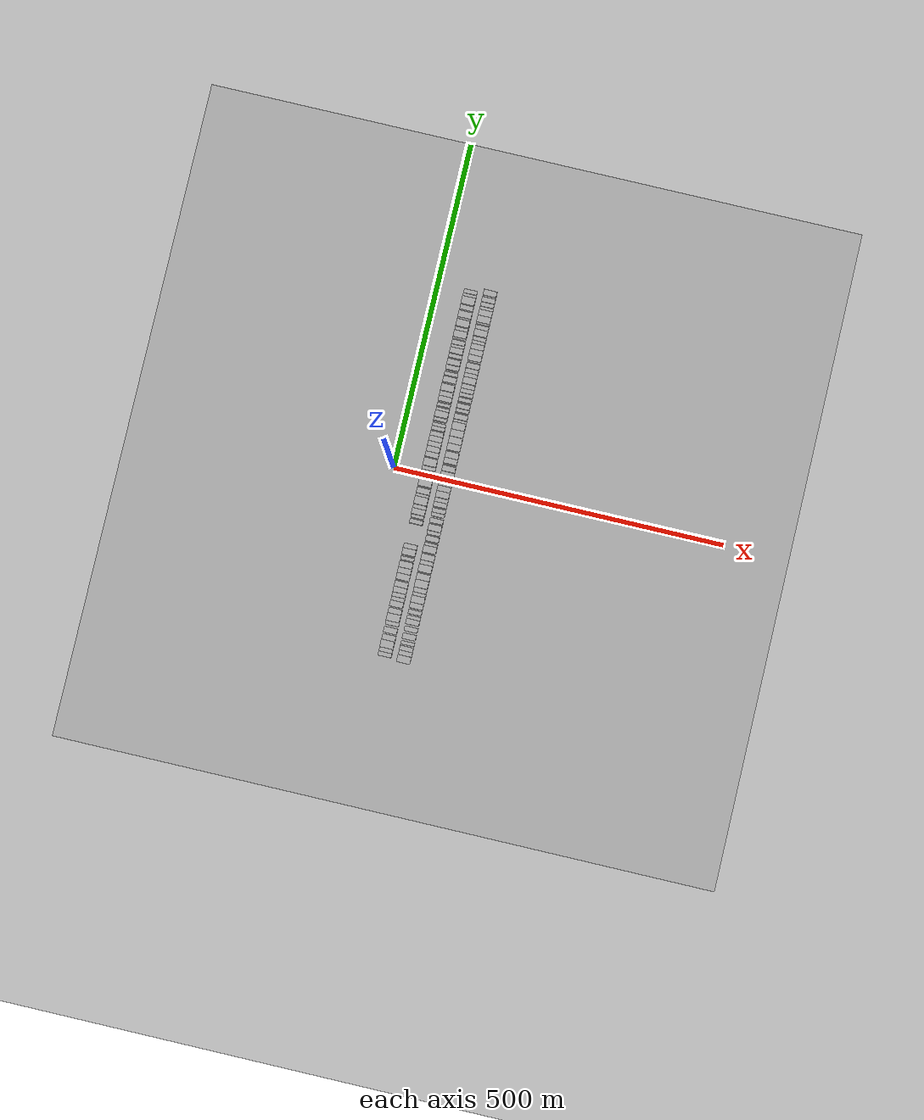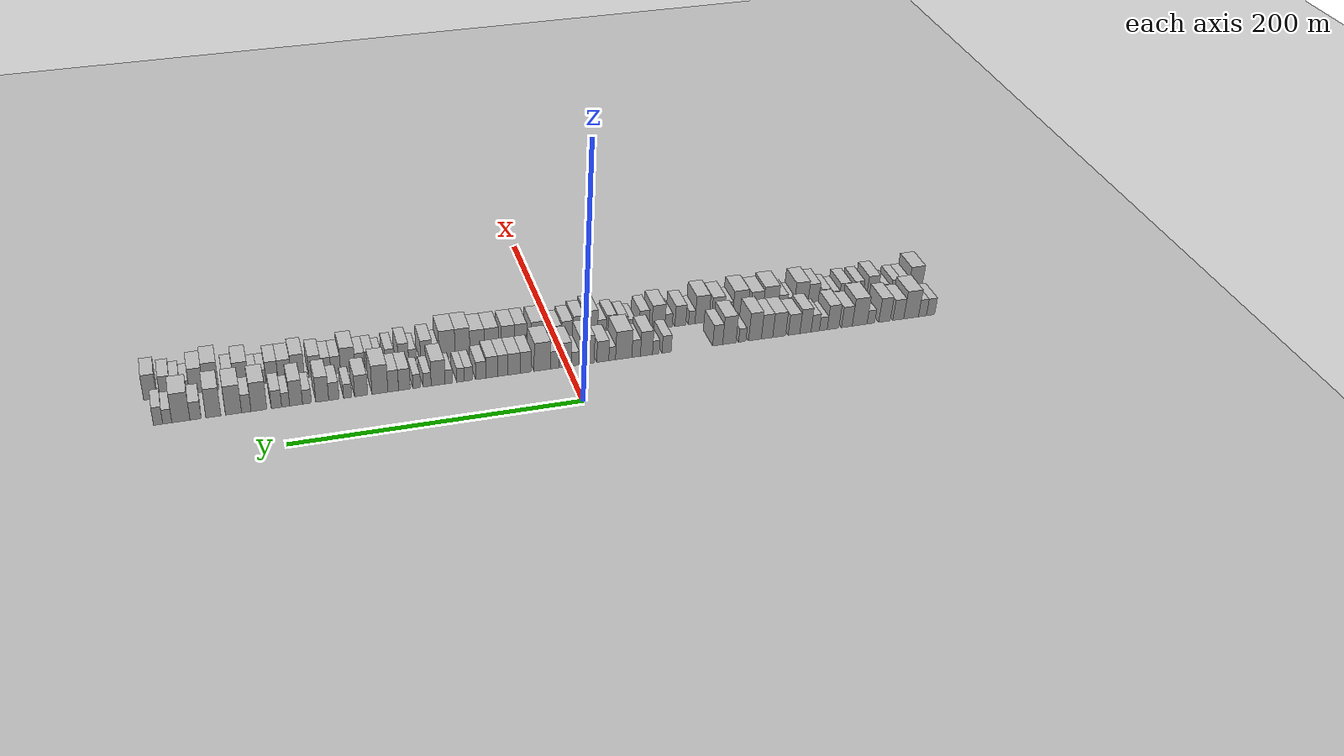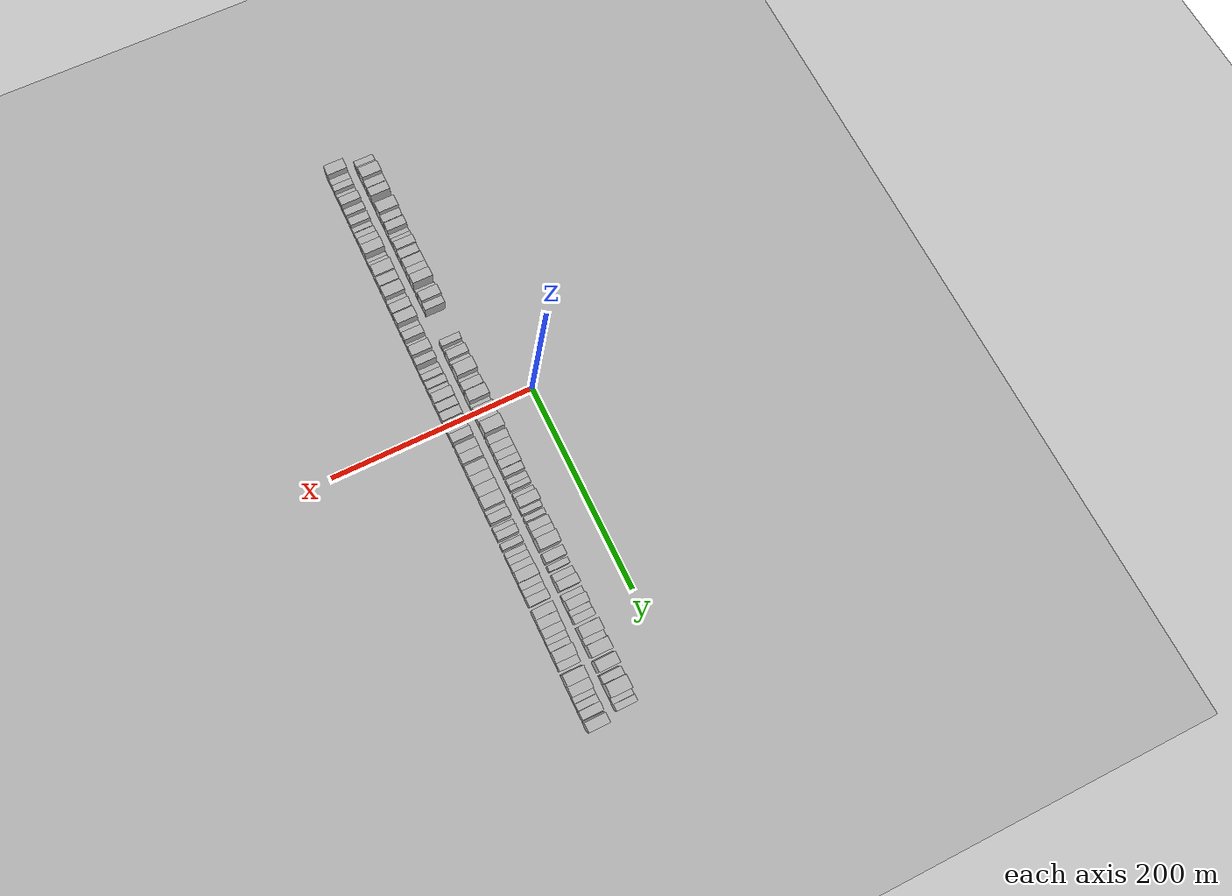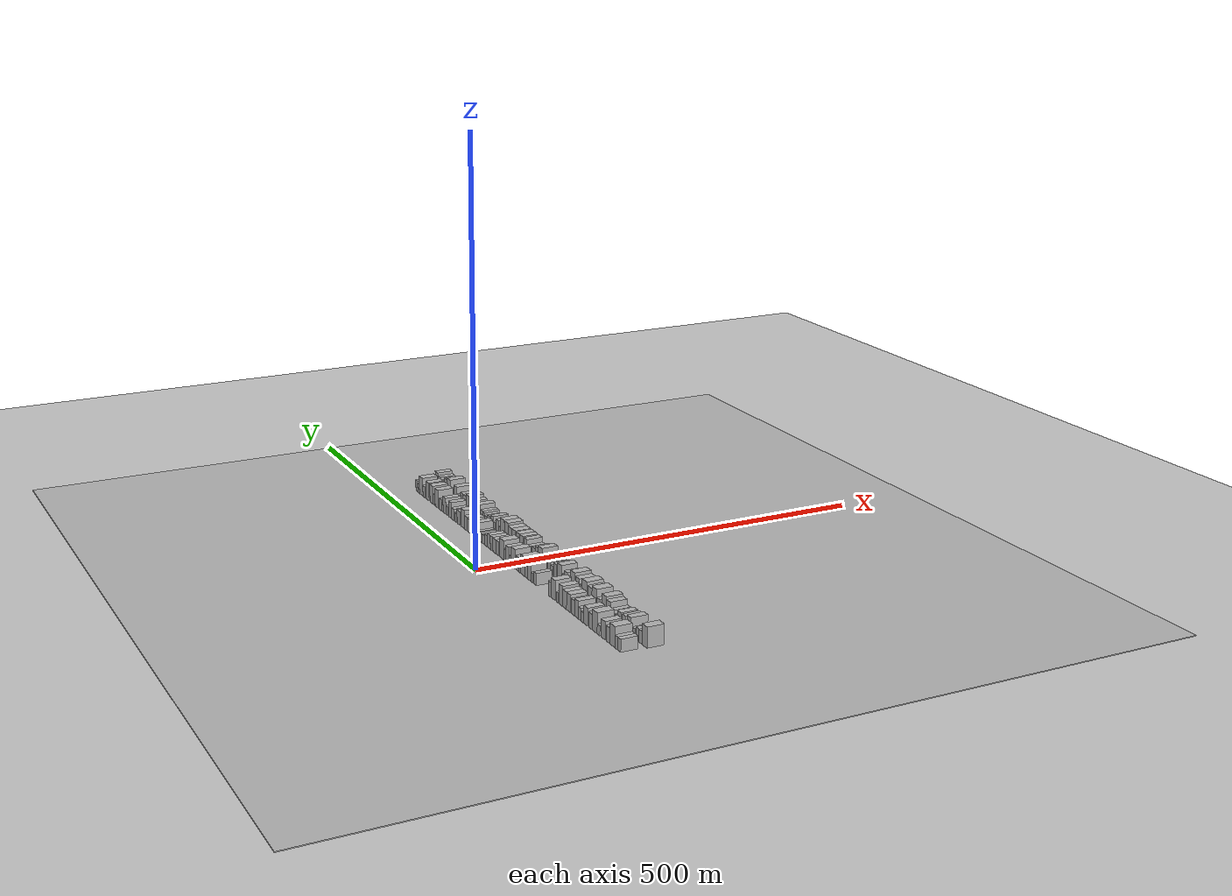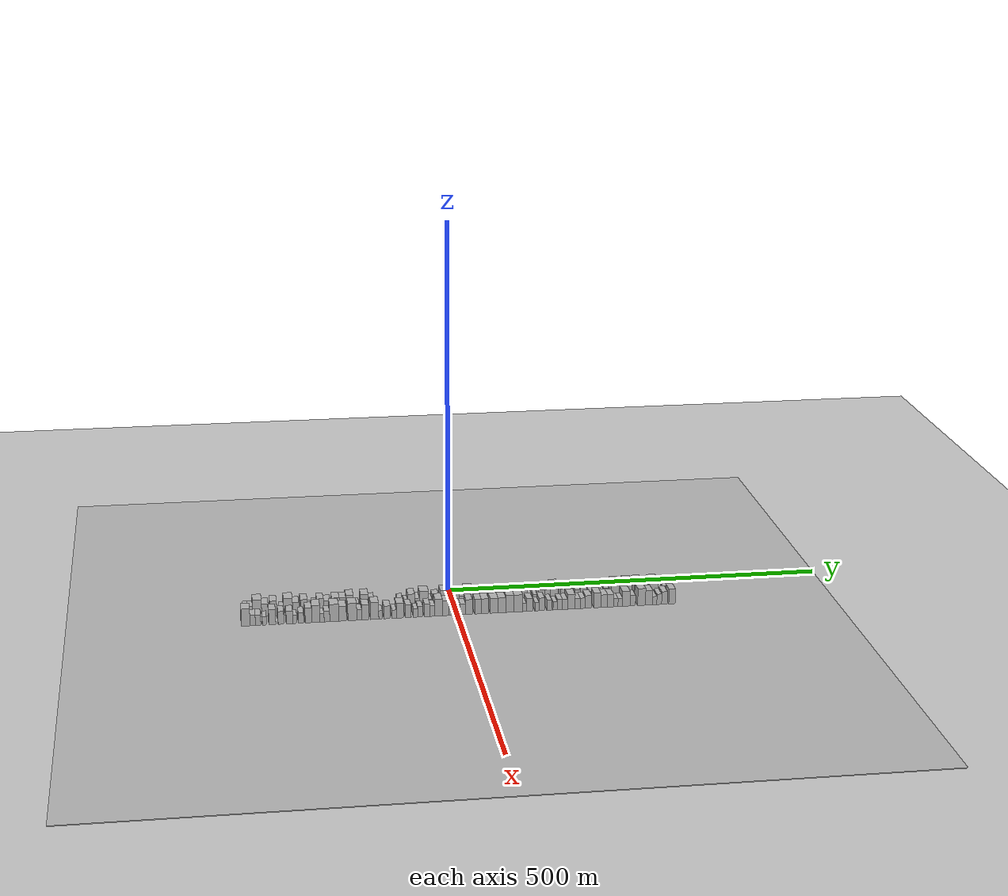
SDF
<?xml version="1.0" encoding="utf-8"?>

<sdf version="1.6">

   <world name="default">

      <gui fullscreen="0">

         <camera name="user_camera">

            <pose>-15 0 4.57585 0 0 0</pose>

            <view_controller>orbit</view_controller>

         </camera>

      </gui>

      <scene>

         <sky>

           <clouds>

             <speed>12</speed>

           </clouds>

         </sky>

         <ambient>0.4 0.4 0.4 1</ambient>

         <background>0.7 0.7 0.7 1</background>

         <shadows>1</shadows>

      </scene>

      <gravity>0 0 -9.8066</gravity>

      <magnetic_field>6e-06 2.3e-05 -4.2e-05</magnetic_field>

      <physics default="0" name="default_physics" type="ode">

         <ode>

            <solver>

               <type>quick</type>

               <iters>10</iters>

               <sor>1.0</sor>

               <use_dynamic_moi_rescaling>0</use_dynamic_moi_rescaling>

            </solver>

            <constraints>

               <cfm>0</cfm>

               <erp>0.2</erp>

               <contact_max_correcting_vel>100</contact_max_correcting_vel>

               <contact_surface_layer>0.001</contact_surface_layer>

            </constraints>

         </ode>

         <max_step_size>0.004</max_step_size>

         <real_time_factor>1</real_time_factor>

         <real_time_update_rate>250</real_time_update_rate>

      </physics>

      <light name="sun" type="directional">

         <cast_shadows>1</cast_shadows>

         <pose>0 0 10 0 0 0</pose>

         <diffuse>0.8 0.8 0.8 1</diffuse>

         <specular>0.2 0.2 0.2 1</specular>

         <attenuation>

            <range>1000</range>

            <constant>0.9</constant>

            <linear>0.01</linear>

            <quadratic>0.001</quadratic>

         </attenuation>

         <direction>-0.5 0.1 -0.9</direction>

      </light>

      <include>

         <name>ground_plane_1</name>

         <uri>model://HANNAS_ground_plane</uri>

         <pose>0 0 0  0 0 0</pose>

      </include>

      <include>

         <name>ground_plane_2</name>

         <uri>model://HANNAS_ground_plane</uri>

         <pose>100 0 0  0 0 0</pose>

      </include>

      <model name="building_1">

         <static>1</static>

         <pose frame="">50.0000 -271.7635 0 0.000000 0.000000 0.000000</pose>

         <link name="link">

            <pose frame="">0 0 7.50 0 0 0</pose>

            <collision name="collision">

               <geometry>

                  <box>

                     <size>20.0000 6.4730 15.0000</size>

                  </box>

               </geometry>

               <max_contacts>10</max_contacts>

               <surface>

                  <contact>

                     <ode/>

                  </contact>

                  <bounce/>

                  <friction>

                     <torsional>

                        <ode/>

                     </torsional>

                     <ode/>

                  </friction>

               </surface>

            </collision>

            <visual name="visual">

               <cast_shadows>0</cast_shadows>

               <geometry>

                  <box>

                     <size>20.0000 6.4730 15.0000</size>

                  </box>

               </geometry>

               <material>

                  <script>

                     <uri>model://HANNAS_wall/materials/scripts</uri>

                     <uri>model://HANNAS_wall/materials/textures</uri>

                     <name>vrc/HANNAS_wall</name>

                  </script>

               </material>

            </visual>

            <self_collide>0</self_collide>

            <enable_wind>0</enable_wind>

            <kinematic>0</kinematic>

         </link>

      </model>

      <model name="building_2">

         <static>1</static>

         <pose frame="">50.0000 -265.3977 0 0.000000 0.000000 0.000000</pose>

         <link name="link">

            <pose frame="">0 0 7.50 0 0 0</pose>

            <collision name="collision">

               <geometry>

                  <box>

                     <size>20.0000 6.2587 15.0000</size>

                  </box>

               </geometry>

               <max_contacts>10</max_contacts>

               <surface>

                  <contact>

                     <ode/>

                  </contact>

                  <bounce/>

                  <friction>

                     <torsional>

                        <ode/>

                     </torsional>

                     <ode/>

                  </friction>

               </surface>

            </collision>

            <visual name="visual">

               <cast_shadows>0</cast_shadows>

               <geometry>

                  <box>

                     <size>20.0000 6.2587 15.0000</size>

                  </box>

               </geometry>

               <material>

                  <script>

                     <uri>model://HANNAS_wall/materials/scripts</uri>

                     <uri>model://HANNAS_wall/materials/textures</uri>

                     <name>vrc/HANNAS_wall</name>

                  </script>

               </material>

            </visual>

            <self_collide>0</self_collide>

            <enable_wind>0</enable_wind>

            <kinematic>0</kinematic>

         </link>

      </model>

      <model name="building_3">

         <static>1</static>

         <pose frame="">50.0000 -256.5157 0 0.000000 0.000000 0.000000</pose>

         <link name="link">

            <pose frame="">0 0 12.00 0 0 0</pose>

            <collision name="collision">

               <geometry>

                  <box>

                     <size>20.0000 11.5051 24.0000</size>

                  </box>

               </geometry>

               <max_contacts>10</max_contacts>

               <surface>

                  <contact>

                     <ode/>

                  </contact>

                  <bounce/>

                  <friction>

                     <torsional>

                        <ode/>

                     </torsional>

                     <ode/>

                  </friction>

               </surface>

            </collision>

            <visual name="visual">

               <cast_shadows>0</cast_shadows>

               <geometry>

                  <box>

                     <size>20.0000 11.5051 24.0000</size>

                  </box>

               </geometry>

               <material>

                  <script>

                     <uri>model://HANNAS_wall/materials/scripts</uri>

                     <uri>model://HANNAS_wall/materials/textures</uri>

                     <name>vrc/HANNAS_wall</name>

                  </script>

               </material>

            </visual>

            <self_collide>0</self_collide>

            <enable_wind>0</enable_wind>

            <kinematic>0</kinematic>

         </link>

      </model>

      <model name="building_4">

         <static>1</static>

         <pose frame="">50.0000 -246.5137 0 0.000000 0.000000 0.000000</pose>

         <link name="link">

            <pose frame="">0 0 9.00 0 0 0</pose>

            <collision name="collision">

               <geometry>

                  <box>

                     <size>20.0000 8.4989 18.0000</size>

                  </box>

               </geometry>

               <max_contacts>10</max_contacts>

               <surface>

                  <contact>

                     <ode/>

                  </contact>

                  <bounce/>

                  <friction>

                     <torsional>

                        <ode/>

                     </torsional>

                     <ode/>

                  </friction>

               </surface>

            </collision>

            <visual name="visual">

               <cast_shadows>0</cast_shadows>

               <geometry>

                  <box>

                     <size>20.0000 8.4989 18.0000</size>

                  </box>

               </geometry>

               <material>

                  <script>

                     <uri>model://HANNAS_wall/materials/scripts</uri>

                     <uri>model://HANNAS_wall/materials/textures</uri>

                     <name>vrc/HANNAS_wall</name>

                  </script>

               </material>

            </visual>

            <self_collide>0</self_collide>

            <enable_wind>0</enable_wind>

            <kinematic>0</kinematic>

         </link>

      </model>

      <model name="building_5">

         <static>1</static>

         <pose frame="">50.0000 -235.7697 0 0.000000 0.000000 0.000000</pose>

         <link name="link">

            <pose frame="">0 0 10.50 0 0 0</pose>

            <collision name="collision">

               <geometry>

                  <box>

                     <size>20.0000 8.9892 21.0000</size>

                  </box>

               </geometry>

               <max_contacts>10</max_contacts>

               <surface>

                  <contact>

                     <ode/>

                  </contact>

                  <bounce/>

                  <friction>

                     <torsional>

                        <ode/>

                     </torsional>

                     <ode/>

                  </friction>

               </surface>

            </collision>

            <visual name="visual">

               <cast_shadows>0</cast_shadows>

               <geometry>

                  <box>

                     <size>20.0000 8.9892 21.0000</size>

                  </box>

               </geometry>

               <material>

                  <script>

                     <uri>model://HANNAS_wall/materials/scripts</uri>

                     <uri>model://HANNAS_wall/materials/textures</uri>

                     <name>vrc/HANNAS_wall</name>

                  </script>

               </material>

            </visual>

            <self_collide>0</self_collide>

            <enable_wind>0</enable_wind>

            <kinematic>0</kinematic>

         </link>

      </model>

      <model name="building_6">

         <static>1</static>

         <pose frame="">50.0000 -225.2756 0 0.000000 0.000000 0.000000</pose>

         <link name="link">

            <pose frame="">0 0 6.00 0 0 0</pose>

            <collision name="collision">

               <geometry>

                  <box>

                     <size>20.0000 5.9991 12.0000</size>

                  </box>

               </geometry>

               <max_contacts>10</max_contacts>

               <surface>

                  <contact>

                     <ode/>

                  </contact>

                  <bounce/>

                  <friction>

                     <torsional>

                        <ode/>

                     </torsional>

                     <ode/>

                  </friction>

               </surface>

            </collision>

            <visual name="visual">

               <cast_shadows>0</cast_shadows>

               <geometry>

                  <box>

                     <size>20.0000 5.9991 12.0000</size>

                  </box>

               </geometry>

               <material>

                  <script>

                     <uri>model://HANNAS_wall/materials/scripts</uri>

                     <uri>model://HANNAS_wall/materials/textures</uri>

                     <name>vrc/HANNAS_wall</name>

                  </script>

               </material>

            </visual>

            <self_collide>0</self_collide>

            <enable_wind>0</enable_wind>

            <kinematic>0</kinematic>

         </link>

      </model>

      <model name="building_7">

         <static>1</static>

         <pose frame="">50.0000 -216.5486 0 0.000000 0.000000 0.000000</pose>

         <link name="link">

            <pose frame="">0 0 12.00 0 0 0</pose>

            <collision name="collision">

               <geometry>

                  <box>

                     <size>20.0000 11.4547 24.0000</size>

                  </box>

               </geometry>

               <max_contacts>10</max_contacts>

               <surface>

                  <contact>

                     <ode/>

                  </contact>

                  <bounce/>

                  <friction>

                     <torsional>

                        <ode/>

                     </torsional>

                     <ode/>

                  </friction>

               </surface>

            </collision>

            <visual name="visual">

               <cast_shadows>0</cast_shadows>

               <geometry>

                  <box>

                     <size>20.0000 11.4547 24.0000</size>

                  </box>

               </geometry>

               <material>

                  <script>

                     <uri>model://HANNAS_wall/materials/scripts</uri>

                     <uri>model://HANNAS_wall/materials/textures</uri>

                     <name>vrc/HANNAS_wall</name>

                  </script>

               </material>

            </visual>

            <self_collide>0</self_collide>

            <enable_wind>0</enable_wind>

            <kinematic>0</kinematic>

         </link>

      </model>

      <model name="building_8">

         <static>1</static>

         <pose frame="">50.0000 -206.6811 0 0.000000 0.000000 0.000000</pose>

         <link name="link">

            <pose frame="">0 0 9.00 0 0 0</pose>

            <collision name="collision">

               <geometry>

                  <box>

                     <size>20.0000 8.2803 18.0000</size>

                  </box>

               </geometry>

               <max_contacts>10</max_contacts>

               <surface>

                  <contact>

                     <ode/>

                  </contact>

                  <bounce/>

                  <friction>

                     <torsional>

                        <ode/>

                     </torsional>

                     <ode/>

                  </friction>

               </surface>

            </collision>

            <visual name="visual">

               <cast_shadows>0</cast_shadows>

               <geometry>

                  <box>

                     <size>20.0000 8.2803 18.0000</size>

                  </box>

               </geometry>

               <material>

                  <script>

                     <uri>model://HANNAS_wall/materials/scripts</uri>

                     <uri>model://HANNAS_wall/materials/textures</uri>

                     <name>vrc/HANNAS_wall</name>

                  </script>

               </material>

            </visual>

            <self_collide>0</self_collide>

            <enable_wind>0</enable_wind>

            <kinematic>0</kinematic>

         </link>

      </model>

      <model name="building_9">

         <static>1</static>

         <pose frame="">50.0000 -196.0445 0 0.000000 0.000000 0.000000</pose>

         <link name="link">

            <pose frame="">0 0 10.50 0 0 0</pose>

            <collision name="collision">

               <geometry>

                  <box>

                     <size>20.0000 8.9930 21.0000</size>

                  </box>

               </geometry>

               <max_contacts>10</max_contacts>

               <surface>

                  <contact>

                     <ode/>

                  </contact>

                  <bounce/>

                  <friction>

                     <torsional>

                        <ode/>

                     </torsional>

                     <ode/>

                  </friction>

               </surface>

            </collision>

            <visual name="visual">

               <cast_shadows>0</cast_shadows>

               <geometry>

                  <box>

                     <size>20.0000 8.9930 21.0000</size>

                  </box>

               </geometry>

               <material>

                  <script>

                     <uri>model://HANNAS_wall/materials/scripts</uri>

                     <uri>model://HANNAS_wall/materials/textures</uri>

                     <name>vrc/HANNAS_wall</name>

                  </script>

               </material>

            </visual>

            <self_collide>0</self_collide>

            <enable_wind>0</enable_wind>

            <kinematic>0</kinematic>

         </link>

      </model>

      <model name="building_10">

         <static>1</static>

         <pose frame="">50.0000 -188.5942 0 0.000000 0.000000 0.000000</pose>

         <link name="link">

            <pose frame="">0 0 6.00 0 0 0</pose>

            <collision name="collision">

               <geometry>

                  <box>

                     <size>20.0000 5.9075 12.0000</size>

                  </box>

               </geometry>

               <max_contacts>10</max_contacts>

               <surface>

                  <contact>

                     <ode/>

                  </contact>

                  <bounce/>

                  <friction>

                     <torsional>

                        <ode/>

                     </torsional>

                     <ode/>

                  </friction>

               </surface>

            </collision>

            <visual name="visual">

               <cast_shadows>0</cast_shadows>

               <geometry>

                  <box>

                     <size>20.0000 5.9075 12.0000</size>

                  </box>

               </geometry>

               <material>

                  <script>

                     <uri>model://HANNAS_wall/materials/scripts</uri>

                     <uri>model://HANNAS_wall/materials/textures</uri>

                     <name>vrc/HANNAS_wall</name>

                  </script>

               </material>

            </visual>

            <self_collide>0</self_collide>

            <enable_wind>0</enable_wind>

            <kinematic>0</kinematic>

         </link>

      </model>

      <model name="building_11">

         <static>1</static>

         <pose frame="">50.0000 -182.4483 0 0.000000 0.000000 0.000000</pose>

         <link name="link">

            <pose frame="">0 0 7.50 0 0 0</pose>

            <collision name="collision">

               <geometry>

                  <box>

                     <size>20.0000 6.3844 15.0000</size>

                  </box>

               </geometry>

               <max_contacts>10</max_contacts>

               <surface>

                  <contact>

                     <ode/>

                  </contact>

                  <bounce/>

                  <friction>

                     <torsional>

                        <ode/>

                     </torsional>

                     <ode/>

                  </friction>

               </surface>

            </collision>

            <visual name="visual">

               <cast_shadows>0</cast_shadows>

               <geometry>

                  <box>

                     <size>20.0000 6.3844 15.0000</size>

                  </box>

               </geometry>

               <material>

                  <script>

                     <uri>model://HANNAS_wall/materials/scripts</uri>

                     <uri>model://HANNAS_wall/materials/textures</uri>

                     <name>vrc/HANNAS_wall</name>

                  </script>

               </material>

            </visual>

            <self_collide>0</self_collide>

            <enable_wind>0</enable_wind>

            <kinematic>0</kinematic>

         </link>

      </model>

      <model name="building_12">

         <static>1</static>

         <pose frame="">50.0000 -174.9815 0 0.000000 0.000000 0.000000</pose>

         <link name="link">

            <pose frame="">0 0 10.50 0 0 0</pose>

            <collision name="collision">

               <geometry>

                  <box>

                     <size>20.0000 8.5493 21.0000</size>

                  </box>

               </geometry>

               <max_contacts>10</max_contacts>

               <surface>

                  <contact>

                     <ode/>

                  </contact>

                  <bounce/>

                  <friction>

                     <torsional>

                        <ode/>

                     </torsional>

                     <ode/>

                  </friction>

               </surface>

            </collision>

            <visual name="visual">

               <cast_shadows>0</cast_shadows>

               <geometry>

                  <box>

                     <size>20.0000 8.5493 21.0000</size>

                  </box>

               </geometry>

               <material>

                  <script>

                     <uri>model://HANNAS_wall/materials/scripts</uri>

                     <uri>model://HANNAS_wall/materials/textures</uri>

                     <name>vrc/HANNAS_wall</name>

                  </script>

               </material>

            </visual>

            <self_collide>0</self_collide>

            <enable_wind>0</enable_wind>

            <kinematic>0</kinematic>

         </link>

      </model>

      <model name="building_13">

         <static>1</static>

         <pose frame="">50.0000 -166.2989 0 0.000000 0.000000 0.000000</pose>

         <link name="link">

            <pose frame="">0 0 9.00 0 0 0</pose>

            <collision name="collision">

               <geometry>

                  <box>

                     <size>20.0000 8.8159 18.0000</size>

                  </box>

               </geometry>

               <max_contacts>10</max_contacts>

               <surface>

                  <contact>

                     <ode/>

                  </contact>

                  <bounce/>

                  <friction>

                     <torsional>

                        <ode/>

                     </torsional>

                     <ode/>

                  </friction>

               </surface>

            </collision>

            <visual name="visual">

               <cast_shadows>0</cast_shadows>

               <geometry>

                  <box>

                     <size>20.0000 8.8159 18.0000</size>

                  </box>

               </geometry>

               <material>

                  <script>

                     <uri>model://HANNAS_wall/materials/scripts</uri>

                     <uri>model://HANNAS_wall/materials/textures</uri>

                     <name>vrc/HANNAS_wall</name>

                  </script>

               </material>

            </visual>

            <self_collide>0</self_collide>

            <enable_wind>0</enable_wind>

            <kinematic>0</kinematic>

         </link>

      </model>

      <model name="building_14">

         <static>1</static>

         <pose frame="">50.0000 -155.0374 0 0.000000 0.000000 0.000000</pose>

         <link name="link">

            <pose frame="">0 0 10.50 0 0 0</pose>

            <collision name="collision">

               <geometry>

                  <box>

                     <size>20.0000 9.7073 21.0000</size>

                  </box>

               </geometry>

               <max_contacts>10</max_contacts>

               <surface>

                  <contact>

                     <ode/>

                  </contact>

                  <bounce/>

                  <friction>

                     <torsional>

                        <ode/>

                     </torsional>

                     <ode/>

                  </friction>

               </surface>

            </collision>

            <visual name="visual">

               <cast_shadows>0</cast_shadows>

               <geometry>

                  <box>

                     <size>20.0000 9.7073 21.0000</size>

                  </box>

               </geometry>

               <material>

                  <script>

                     <uri>model://HANNAS_wall/materials/scripts</uri>

                     <uri>model://HANNAS_wall/materials/textures</uri>

                     <name>vrc/HANNAS_wall</name>

                  </script>

               </material>

            </visual>

            <self_collide>0</self_collide>

            <enable_wind>0</enable_wind>

            <kinematic>0</kinematic>

         </link>

      </model>

      <model name="building_15">

         <static>1</static>

         <pose frame="">50.0000 -145.8788 0 0.000000 0.000000 0.000000</pose>

         <link name="link">

            <pose frame="">0 0 10.50 0 0 0</pose>

            <collision name="collision">

               <geometry>

                  <box>

                     <size>20.0000 8.6098 21.0000</size>

                  </box>

               </geometry>

               <max_contacts>10</max_contacts>

               <surface>

                  <contact>

                     <ode/>

                  </contact>

                  <bounce/>

                  <friction>

                     <torsional>

                        <ode/>

                     </torsional>

                     <ode/>

                  </friction>

               </surface>

            </collision>

            <visual name="visual">

               <cast_shadows>0</cast_shadows>

               <geometry>

                  <box>

                     <size>20.0000 8.6098 21.0000</size>

                  </box>

               </geometry>

               <material>

                  <script>

                     <uri>model://HANNAS_wall/materials/scripts</uri>

                     <uri>model://HANNAS_wall/materials/textures</uri>

                     <name>vrc/HANNAS_wall</name>

                  </script>

               </material>

            </visual>

            <self_collide>0</self_collide>

            <enable_wind>0</enable_wind>

            <kinematic>0</kinematic>

         </link>

      </model>

      <model name="building_16">

         <static>1</static>

         <pose frame="">50.0000 -136.7682 0 0.000000 0.000000 0.000000</pose>

         <link name="link">

            <pose frame="">0 0 12.00 0 0 0</pose>

            <collision name="collision">

               <geometry>

                  <box>

                     <size>20.0000 9.6115 24.0000</size>

                  </box>

               </geometry>

               <max_contacts>10</max_contacts>

               <surface>

                  <contact>

                     <ode/>

                  </contact>

                  <bounce/>

                  <friction>

                     <torsional>

                        <ode/>

                     </torsional>

                     <ode/>

                  </friction>

               </surface>

            </collision>

            <visual name="visual">

               <cast_shadows>0</cast_shadows>

               <geometry>

                  <box>

                     <size>20.0000 9.6115 24.0000</size>

                  </box>

               </geometry>

               <material>

                  <script>

                     <uri>model://HANNAS_wall/materials/scripts</uri>

                     <uri>model://HANNAS_wall/materials/textures</uri>

                     <name>vrc/HANNAS_wall</name>

                  </script>

               </material>

            </visual>

            <self_collide>0</self_collide>

            <enable_wind>0</enable_wind>

            <kinematic>0</kinematic>

         </link>

      </model>

      <model name="building_17">

         <static>1</static>

         <pose frame="">50.0000 -127.2424 0 0.000000 0.000000 0.000000</pose>

         <link name="link">

            <pose frame="">0 0 6.00 0 0 0</pose>

            <collision name="collision">

               <geometry>

                  <box>

                     <size>20.0000 5.4399 12.0000</size>

                  </box>

               </geometry>

               <max_contacts>10</max_contacts>

               <surface>

                  <contact>

                     <ode/>

                  </contact>

                  <bounce/>

                  <friction>

                     <torsional>

                        <ode/>

                     </torsional>

                     <ode/>

                  </friction>

               </surface>

            </collision>

            <visual name="visual">

               <cast_shadows>0</cast_shadows>

               <geometry>

                  <box>

                     <size>20.0000 5.4399 12.0000</size>

                  </box>

               </geometry>

               <material>

                  <script>

                     <uri>model://HANNAS_wall/materials/scripts</uri>

                     <uri>model://HANNAS_wall/materials/textures</uri>

                     <name>vrc/HANNAS_wall</name>

                  </script>

               </material>

            </visual>

            <self_collide>0</self_collide>

            <enable_wind>0</enable_wind>

            <kinematic>0</kinematic>

         </link>

      </model>

      <model name="building_18">

         <static>1</static>

         <pose frame="">50.0000 -117.5544 0 0.000000 0.000000 0.000000</pose>

         <link name="link">

            <pose frame="">0 0 12.00 0 0 0</pose>

            <collision name="collision">

               <geometry>

                  <box>

                     <size>20.0000 9.9362 24.0000</size>

                  </box>

               </geometry>

               <max_contacts>10</max_contacts>

               <surface>

                  <contact>

                     <ode/>

                  </contact>

                  <bounce/>

                  <friction>

                     <torsional>

                        <ode/>

                     </torsional>

                     <ode/>

                  </friction>

               </surface>

            </collision>

            <visual name="visual">

               <cast_shadows>0</cast_shadows>

               <geometry>

                  <box>

                     <size>20.0000 9.9362 24.0000</size>

                  </box>

               </geometry>

               <material>

                  <script>

                     <uri>model://HANNAS_wall/materials/scripts</uri>

                     <uri>model://HANNAS_wall/materials/textures</uri>

                     <name>vrc/HANNAS_wall</name>

                  </script>

               </material>

            </visual>

            <self_collide>0</self_collide>

            <enable_wind>0</enable_wind>

            <kinematic>0</kinematic>

         </link>

      </model>

      <model name="building_19">

         <static>1</static>

         <pose frame="">50.0000 -108.8718 0 0.000000 0.000000 0.000000</pose>

         <link name="link">

            <pose frame="">0 0 9.00 0 0 0</pose>

            <collision name="collision">

               <geometry>

                  <box>

                     <size>20.0000 7.4288 18.0000</size>

                  </box>

               </geometry>

               <max_contacts>10</max_contacts>

               <surface>

                  <contact>

                     <ode/>

                  </contact>

                  <bounce/>

                  <friction>

                     <torsional>

                        <ode/>

                     </torsional>

                     <ode/>

                  </friction>

               </surface>

            </collision>

            <visual name="visual">

               <cast_shadows>0</cast_shadows>

               <geometry>

                  <box>

                     <size>20.0000 7.4288 18.0000</size>

                  </box>

               </geometry>

               <material>

                  <script>

                     <uri>model://HANNAS_wall/materials/scripts</uri>

                     <uri>model://HANNAS_wall/materials/textures</uri>

                     <name>vrc/HANNAS_wall</name>

                  </script>

               </material>

            </visual>

            <self_collide>0</self_collide>

            <enable_wind>0</enable_wind>

            <kinematic>0</kinematic>

         </link>

      </model>

      <model name="building_20">

         <static>1</static>

         <pose frame="">50.0000 -71.0486 0 0.000000 0.000000 0.000000</pose>

         <link name="link">

            <pose frame="">0 0 7.50 0 0 0</pose>

            <collision name="collision">

               <geometry>

                  <box>

                     <size>20.0000 6.7392 15.0000</size>

                  </box>

               </geometry>

               <max_contacts>10</max_contacts>

               <surface>

                  <contact>

                     <ode/>

                  </contact>

                  <bounce/>

                  <friction>

                     <torsional>

                        <ode/>

                     </torsional>

                     <ode/>

                  </friction>

               </surface>

            </collision>

            <visual name="visual">

               <cast_shadows>0</cast_shadows>

               <geometry>

                  <box>

                     <size>20.0000 6.7392 15.0000</size>

                  </box>

               </geometry>

               <material>

                  <script>

                     <uri>model://HANNAS_wall/materials/scripts</uri>

                     <uri>model://HANNAS_wall/materials/textures</uri>

                     <name>vrc/HANNAS_wall</name>

                  </script>

               </material>

            </visual>

            <self_collide>0</self_collide>

            <enable_wind>0</enable_wind>

            <kinematic>0</kinematic>

         </link>

      </model>

      <model name="building_21">

         <static>1</static>

         <pose frame="">50.0000 -63.2042 0 0.000000 0.000000 0.000000</pose>

         <link name="link">

            <pose frame="">0 0 6.00 0 0 0</pose>

            <collision name="collision">

               <geometry>

                  <box>

                     <size>20.0000 4.9497 12.0000</size>

                  </box>

               </geometry>

               <max_contacts>10</max_contacts>

               <surface>

                  <contact>

                     <ode/>

                  </contact>

                  <bounce/>

                  <friction>

                     <torsional>

                        <ode/>

                     </torsional>

                     <ode/>

                  </friction>

               </surface>

            </collision>

            <visual name="visual">

               <cast_shadows>0</cast_shadows>

               <geometry>

                  <box>

                     <size>20.0000 4.9497 12.0000</size>

                  </box>

               </geometry>

               <material>

                  <script>

                     <uri>model://HANNAS_wall/materials/scripts</uri>

                     <uri>model://HANNAS_wall/materials/textures</uri>

                     <name>vrc/HANNAS_wall</name>

                  </script>

               </material>

            </visual>

            <self_collide>0</self_collide>

            <enable_wind>0</enable_wind>

            <kinematic>0</kinematic>

         </link>

      </model>

      <model name="building_22">

         <static>1</static>

         <pose frame="">50.0000 -56.3069 0 0.000000 0.000000 0.000000</pose>

         <link name="link">

            <pose frame="">0 0 10.50 0 0 0</pose>

            <collision name="collision">

               <geometry>

                  <box>

                     <size>20.0000 8.8449 21.0000</size>

                  </box>

               </geometry>

               <max_contacts>10</max_contacts>

               <surface>

                  <contact>

                     <ode/>

                  </contact>

                  <bounce/>

                  <friction>

                     <torsional>

                        <ode/>

                     </torsional>

                     <ode/>

                  </friction>

               </surface>

            </collision>

            <visual name="visual">

               <cast_shadows>0</cast_shadows>

               <geometry>

                  <box>

                     <size>20.0000 8.8449 21.0000</size>

                  </box>

               </geometry>

               <material>

                  <script>

                     <uri>model://HANNAS_wall/materials/scripts</uri>

                     <uri>model://HANNAS_wall/materials/textures</uri>

                     <name>vrc/HANNAS_wall</name>

                  </script>

               </material>

            </visual>

            <self_collide>0</self_collide>

            <enable_wind>0</enable_wind>

            <kinematic>0</kinematic>

         </link>

      </model>

      <model name="building_23">

         <static>1</static>

         <pose frame="">50.0000 -48.7572 0 0.000000 0.000000 0.000000</pose>

         <link name="link">

            <pose frame="">0 0 7.50 0 0 0</pose>

            <collision name="collision">

               <geometry>

                  <box>

                     <size>20.0000 6.2545 15.0000</size>

                  </box>

               </geometry>

               <max_contacts>10</max_contacts>

               <surface>

                  <contact>

                     <ode/>

                  </contact>

                  <bounce/>

                  <friction>

                     <torsional>

                        <ode/>

                     </torsional>

                     <ode/>

                  </friction>

               </surface>

            </collision>

            <visual name="visual">

               <cast_shadows>0</cast_shadows>

               <geometry>

                  <box>

                     <size>20.0000 6.2545 15.0000</size>

                  </box>

               </geometry>

               <material>

                  <script>

                     <uri>model://HANNAS_wall/materials/scripts</uri>

                     <uri>model://HANNAS_wall/materials/textures</uri>

                     <name>vrc/HANNAS_wall</name>

                  </script>

               </material>

            </visual>

            <self_collide>0</self_collide>

            <enable_wind>0</enable_wind>

            <kinematic>0</kinematic>

         </link>

      </model>

      <model name="building_24">

         <static>1</static>

         <pose frame="">50.0000 -39.6794 0 0.000000 0.000000 0.000000</pose>

         <link name="link">

            <pose frame="">0 0 12.00 0 0 0</pose>

            <collision name="collision">

               <geometry>

                  <box>

                     <size>20.0000 11.9011 24.0000</size>

                  </box>

               </geometry>

               <max_contacts>10</max_contacts>

               <surface>

                  <contact>

                     <ode/>

                  </contact>

                  <bounce/>

                  <friction>

                     <torsional>

                        <ode/>

                     </torsional>

                     <ode/>

                  </friction>

               </surface>

            </collision>

            <visual name="visual">

               <cast_shadows>0</cast_shadows>

               <geometry>

                  <box>

                     <size>20.0000 11.9011 24.0000</size>

                  </box>

               </geometry>

               <material>

                  <script>

                     <uri>model://HANNAS_wall/materials/scripts</uri>

                     <uri>model://HANNAS_wall/materials/textures</uri>

                     <name>vrc/HANNAS_wall</name>

                  </script>

               </material>

            </visual>

            <self_collide>0</self_collide>

            <enable_wind>0</enable_wind>

            <kinematic>0</kinematic>

         </link>

      </model>

      <model name="building_25">

         <static>1</static>

         <pose frame="">50.0000 -31.2915 0 0.000000 0.000000 0.000000</pose>

         <link name="link">

            <pose frame="">0 0 6.00 0 0 0</pose>

            <collision name="collision">

               <geometry>

                  <box>

                     <size>20.0000 4.8747 12.0000</size>

                  </box>

               </geometry>

               <max_contacts>10</max_contacts>

               <surface>

                  <contact>

                     <ode/>

                  </contact>

                  <bounce/>

                  <friction>

                     <torsional>

                        <ode/>

                     </torsional>

                     <ode/>

                  </friction>

               </surface>

            </collision>

            <visual name="visual">

               <cast_shadows>0</cast_shadows>

               <geometry>

                  <box>

                     <size>20.0000 4.8747 12.0000</size>

                  </box>

               </geometry>

               <material>

                  <script>

                     <uri>model://HANNAS_wall/materials/scripts</uri>

                     <uri>model://HANNAS_wall/materials/textures</uri>

                     <name>vrc/HANNAS_wall</name>

                  </script>

               </material>

            </visual>

            <self_collide>0</self_collide>

            <enable_wind>0</enable_wind>

            <kinematic>0</kinematic>

         </link>

      </model>

      <model name="building_26">

         <static>1</static>

         <pose frame="">50.0000 -24.5110 0 0.000000 0.000000 0.000000</pose>

         <link name="link">

            <pose frame="">0 0 9.00 0 0 0</pose>

            <collision name="collision">

               <geometry>

                  <box>

                     <size>20.0000 8.6863 18.0000</size>

                  </box>

               </geometry>

               <max_contacts>10</max_contacts>

               <surface>

                  <contact>

                     <ode/>

                  </contact>

                  <bounce/>

                  <friction>

                     <torsional>

                        <ode/>

                     </torsional>

                     <ode/>

                  </friction>

               </surface>

            </collision>

            <visual name="visual">

               <cast_shadows>0</cast_shadows>

               <geometry>

                  <box>

                     <size>20.0000 8.6863 18.0000</size>

                  </box>

               </geometry>

               <material>

                  <script>

                     <uri>model://HANNAS_wall/materials/scripts</uri>

                     <uri>model://HANNAS_wall/materials/textures</uri>

                     <name>vrc/HANNAS_wall</name>

                  </script>

               </material>

            </visual>

            <self_collide>0</self_collide>

            <enable_wind>0</enable_wind>

            <kinematic>0</kinematic>

         </link>

      </model>

      <model name="building_27">

         <static>1</static>

         <pose frame="">50.0000 -12.8397 0 0.000000 0.000000 0.000000</pose>

         <link name="link">

            <pose frame="">0 0 12.00 0 0 0</pose>

            <collision name="collision">

               <geometry>

                  <box>

                     <size>20.0000 10.6564 24.0000</size>

                  </box>

               </geometry>

               <max_contacts>10</max_contacts>

               <surface>

                  <contact>

                     <ode/>

                  </contact>

                  <bounce/>

                  <friction>

                     <torsional>

                        <ode/>

                     </torsional>

                     <ode/>

                  </friction>

               </surface>

            </collision>

            <visual name="visual">

               <cast_shadows>0</cast_shadows>

               <geometry>

                  <box>

                     <size>20.0000 10.6564 24.0000</size>

                  </box>

               </geometry>

               <material>

                  <script>

                     <uri>model://HANNAS_wall/materials/scripts</uri>

                     <uri>model://HANNAS_wall/materials/textures</uri>

                     <name>vrc/HANNAS_wall</name>

                  </script>

               </material>

            </visual>

            <self_collide>0</self_collide>

            <enable_wind>0</enable_wind>

            <kinematic>0</kinematic>

         </link>

      </model>

      <model name="building_28">

         <static>1</static>

         <pose frame="">50.0000 -4.6544 0 0.000000 0.000000 0.000000</pose>

         <link name="link">

            <pose frame="">0 0 6.00 0 0 0</pose>

            <collision name="collision">

               <geometry>

                  <box>

                     <size>20.0000 5.7142 12.0000</size>

                  </box>

               </geometry>

               <max_contacts>10</max_contacts>

               <surface>

                  <contact>

                     <ode/>

                  </contact>

                  <bounce/>

                  <friction>

                     <torsional>

                        <ode/>

                     </torsional>

                     <ode/>

                  </friction>

               </surface>

            </collision>

            <visual name="visual">

               <cast_shadows>0</cast_shadows>

               <geometry>

                  <box>

                     <size>20.0000 5.7142 12.0000</size>

                  </box>

               </geometry>

               <material>

                  <script>

                     <uri>model://HANNAS_wall/materials/scripts</uri>

                     <uri>model://HANNAS_wall/materials/textures</uri>

                     <name>vrc/HANNAS_wall</name>

                  </script>

               </material>

            </visual>

            <self_collide>0</self_collide>

            <enable_wind>0</enable_wind>

            <kinematic>0</kinematic>

         </link>

      </model>

      <model name="building_29">

         <static>1</static>

         <pose frame="">50.0000 2.5141 0 0.000000 0.000000 0.000000</pose>

         <link name="link">

            <pose frame="">0 0 10.50 0 0 0</pose>

            <collision name="collision">

               <geometry>

                  <box>

                     <size>20.0000 8.6228 21.0000</size>

                  </box>

               </geometry>

               <max_contacts>10</max_contacts>

               <surface>

                  <contact>

                     <ode/>

                  </contact>

                  <bounce/>

                  <friction>

                     <torsional>

                        <ode/>

                     </torsional>

                     <ode/>

                  </friction>

               </surface>

            </collision>

            <visual name="visual">

               <cast_shadows>0</cast_shadows>

               <geometry>

                  <box>

                     <size>20.0000 8.6228 21.0000</size>

                  </box>

               </geometry>

               <material>

                  <script>

                     <uri>model://HANNAS_wall/materials/scripts</uri>

                     <uri>model://HANNAS_wall/materials/textures</uri>

                     <name>vrc/HANNAS_wall</name>

                  </script>

               </material>

            </visual>

            <self_collide>0</self_collide>

            <enable_wind>0</enable_wind>

            <kinematic>0</kinematic>

         </link>

      </model>

      <model name="building_30">

         <static>1</static>

         <pose frame="">50.0000 9.9196 0 0.000000 0.000000 0.000000</pose>

         <link name="link">

            <pose frame="">0 0 7.50 0 0 0</pose>

            <collision name="collision">

               <geometry>

                  <box>

                     <size>20.0000 6.1883 15.0000</size>

                  </box>

               </geometry>

               <max_contacts>10</max_contacts>

               <surface>

                  <contact>

                     <ode/>

                  </contact>

                  <bounce/>

                  <friction>

                     <torsional>

                        <ode/>

                     </torsional>

                     <ode/>

                  </friction>

               </surface>

            </collision>

            <visual name="visual">

               <cast_shadows>0</cast_shadows>

               <geometry>

                  <box>

                     <size>20.0000 6.1883 15.0000</size>

                  </box>

               </geometry>

               <material>

                  <script>

                     <uri>model://HANNAS_wall/materials/scripts</uri>

                     <uri>model://HANNAS_wall/materials/textures</uri>

                     <name>vrc/HANNAS_wall</name>

                  </script>

               </material>

            </visual>

            <self_collide>0</self_collide>

            <enable_wind>0</enable_wind>

            <kinematic>0</kinematic>

         </link>

      </model>

      <model name="building_31">

         <static>1</static>

         <pose frame="">50.0000 18.8961 0 0.000000 0.000000 0.000000</pose>

         <link name="link">

            <pose frame="">0 0 12.00 0 0 0</pose>

            <collision name="collision">

               <geometry>

                  <box>

                     <size>20.0000 11.7647 24.0000</size>

                  </box>

               </geometry>

               <max_contacts>10</max_contacts>

               <surface>

                  <contact>

                     <ode/>

                  </contact>

                  <bounce/>

                  <friction>

                     <torsional>

                        <ode/>

                     </torsional>

                     <ode/>

                  </friction>

               </surface>

            </collision>

            <visual name="visual">

               <cast_shadows>0</cast_shadows>

               <geometry>

                  <box>

                     <size>20.0000 11.7647 24.0000</size>

                  </box>

               </geometry>

               <material>

                  <script>

                     <uri>model://HANNAS_wall/materials/scripts</uri>

                     <uri>model://HANNAS_wall/materials/textures</uri>

                     <name>vrc/HANNAS_wall</name>

                  </script>

               </material>

            </visual>

            <self_collide>0</self_collide>

            <enable_wind>0</enable_wind>

            <kinematic>0</kinematic>

         </link>

      </model>

      <model name="building_32">

         <static>1</static>

         <pose frame="">50.0000 30.7155 0 0.000000 0.000000 0.000000</pose>

         <link name="link">

            <pose frame="">0 0 9.00 0 0 0</pose>

            <collision name="collision">

               <geometry>

                  <box>

                     <size>20.0000 7.8740 18.0000</size>

                  </box>

               </geometry>

               <max_contacts>10</max_contacts>

               <surface>

                  <contact>

                     <ode/>

                  </contact>

                  <bounce/>

                  <friction>

                     <torsional>

                        <ode/>

                     </torsional>

                     <ode/>

                  </friction>

               </surface>

            </collision>

            <visual name="visual">

               <cast_shadows>0</cast_shadows>

               <geometry>

                  <box>

                     <size>20.0000 7.8740 18.0000</size>

                  </box>

               </geometry>

               <material>

                  <script>

                     <uri>model://HANNAS_wall/materials/scripts</uri>

                     <uri>model://HANNAS_wall/materials/textures</uri>

                     <name>vrc/HANNAS_wall</name>

                  </script>

               </material>

            </visual>

            <self_collide>0</self_collide>

            <enable_wind>0</enable_wind>

            <kinematic>0</kinematic>

         </link>

      </model>

      <model name="building_33">

         <static>1</static>

         <pose frame="">50.0000 38.9766 0 0.000000 0.000000 0.000000</pose>

         <link name="link">

            <pose frame="">0 0 9.00 0 0 0</pose>

            <collision name="collision">

               <geometry>

                  <box>

                     <size>20.0000 8.6483 18.0000</size>

                  </box>

               </geometry>

               <max_contacts>10</max_contacts>

               <surface>

                  <contact>

                     <ode/>

                  </contact>

                  <bounce/>

                  <friction>

                     <torsional>

                        <ode/>

                     </torsional>

                     <ode/>

                  </friction>

               </surface>

            </collision>

            <visual name="visual">

               <cast_shadows>0</cast_shadows>

               <geometry>

                  <box>

                     <size>20.0000 8.6483 18.0000</size>

                  </box>

               </geometry>

               <material>

                  <script>

                     <uri>model://HANNAS_wall/materials/scripts</uri>

                     <uri>model://HANNAS_wall/materials/textures</uri>

                     <name>vrc/HANNAS_wall</name>

                  </script>

               </material>

            </visual>

            <self_collide>0</self_collide>

            <enable_wind>0</enable_wind>

            <kinematic>0</kinematic>

         </link>

      </model>

      <model name="building_34">

         <static>1</static>

         <pose frame="">50.0000 46.9792 0 0.000000 0.000000 0.000000</pose>

         <link name="link">

            <pose frame="">0 0 9.00 0 0 0</pose>

            <collision name="collision">

               <geometry>

                  <box>

                     <size>20.0000 7.3569 18.0000</size>

                  </box>

               </geometry>

               <max_contacts>10</max_contacts>

               <surface>

                  <contact>

                     <ode/>

                  </contact>

                  <bounce/>

                  <friction>

                     <torsional>

                        <ode/>

                     </torsional>

                     <ode/>

                  </friction>

               </surface>

            </collision>

            <visual name="visual">

               <cast_shadows>0</cast_shadows>

               <geometry>

                  <box>

                     <size>20.0000 7.3569 18.0000</size>

                  </box>

               </geometry>

               <material>

                  <script>

                     <uri>model://HANNAS_wall/materials/scripts</uri>

                     <uri>model://HANNAS_wall/materials/textures</uri>

                     <name>vrc/HANNAS_wall</name>

                  </script>

               </material>

            </visual>

            <self_collide>0</self_collide>

            <enable_wind>0</enable_wind>

            <kinematic>0</kinematic>

         </link>

      </model>

      <model name="building_35">

         <static>1</static>

         <pose frame="">50.0000 54.7420 0 0.000000 0.000000 0.000000</pose>

         <link name="link">

            <pose frame="">0 0 9.00 0 0 0</pose>

            <collision name="collision">

               <geometry>

                  <box>

                     <size>20.0000 8.1687 18.0000</size>

                  </box>

               </geometry>

               <max_contacts>10</max_contacts>

               <surface>

                  <contact>

                     <ode/>

                  </contact>

                  <bounce/>

                  <friction>

                     <torsional>

                        <ode/>

                     </torsional>

                     <ode/>

                  </friction>

               </surface>

            </collision>

            <visual name="visual">

               <cast_shadows>0</cast_shadows>

               <geometry>

                  <box>

                     <size>20.0000 8.1687 18.0000</size>

                  </box>

               </geometry>

               <material>

                  <script>

                     <uri>model://HANNAS_wall/materials/scripts</uri>

                     <uri>model://HANNAS_wall/materials/textures</uri>

                     <name>vrc/HANNAS_wall</name>

                  </script>

               </material>

            </visual>

            <self_collide>0</self_collide>

            <enable_wind>0</enable_wind>

            <kinematic>0</kinematic>

         </link>

      </model>

      <model name="building_36">

         <static>1</static>

         <pose frame="">50.0000 62.4307 0 0.000000 0.000000 0.000000</pose>

         <link name="link">

            <pose frame="">0 0 7.50 0 0 0</pose>

            <collision name="collision">

               <geometry>

                  <box>

                     <size>20.0000 7.2087 15.0000</size>

                  </box>

               </geometry>

               <max_contacts>10</max_contacts>

               <surface>

                  <contact>

                     <ode/>

                  </contact>

                  <bounce/>

                  <friction>

                     <torsional>

                        <ode/>

                     </torsional>

                     <ode/>

                  </friction>

               </surface>

            </collision>

            <visual name="visual">

               <cast_shadows>0</cast_shadows>

               <geometry>

                  <box>

                     <size>20.0000 7.2087 15.0000</size>

                  </box>

               </geometry>

               <material>

                  <script>

                     <uri>model://HANNAS_wall/materials/scripts</uri>

                     <uri>model://HANNAS_wall/materials/textures</uri>

                     <name>vrc/HANNAS_wall</name>

                  </script>

               </material>

            </visual>

            <self_collide>0</self_collide>

            <enable_wind>0</enable_wind>

            <kinematic>0</kinematic>

         </link>

      </model>

      <model name="building_37">

         <static>1</static>

         <pose frame="">50.0000 71.0295 0 0.000000 0.000000 0.000000</pose>

         <link name="link">

            <pose frame="">0 0 6.00 0 0 0</pose>

            <collision name="collision">

               <geometry>

                  <box>

                     <size>20.0000 5.9889 12.0000</size>

                  </box>

               </geometry>

               <max_contacts>10</max_contacts>

               <surface>

                  <contact>

                     <ode/>

                  </contact>

                  <bounce/>

                  <friction>

                     <torsional>

                        <ode/>

                     </torsional>

                     <ode/>

                  </friction>

               </surface>

            </collision>

            <visual name="visual">

               <cast_shadows>0</cast_shadows>

               <geometry>

                  <box>

                     <size>20.0000 5.9889 12.0000</size>

                  </box>

               </geometry>

               <material>

                  <script>

                     <uri>model://HANNAS_wall/materials/scripts</uri>

                     <uri>model://HANNAS_wall/materials/textures</uri>

                     <name>vrc/HANNAS_wall</name>

                  </script>

               </material>

            </visual>

            <self_collide>0</self_collide>

            <enable_wind>0</enable_wind>

            <kinematic>0</kinematic>

         </link>

      </model>

      <model name="building_38">

         <static>1</static>

         <pose frame="">50.0000 76.6315 0 0.000000 0.000000 0.000000</pose>

         <link name="link">

            <pose frame="">0 0 6.00 0 0 0</pose>

            <collision name="collision">

               <geometry>

                  <box>

                     <size>20.0000 5.2150 12.0000</size>

                  </box>

               </geometry>

               <max_contacts>10</max_contacts>

               <surface>

                  <contact>

                     <ode/>

                  </contact>

                  <bounce/>

                  <friction>

                     <torsional>

                        <ode/>

                     </torsional>

                     <ode/>

                  </friction>

               </surface>

            </collision>

            <visual name="visual">

               <cast_shadows>0</cast_shadows>

               <geometry>

                  <box>

                     <size>20.0000 5.2150 12.0000</size>

                  </box>

               </geometry>

               <material>

                  <script>

                     <uri>model://HANNAS_wall/materials/scripts</uri>

                     <uri>model://HANNAS_wall/materials/textures</uri>

                     <name>vrc/HANNAS_wall</name>

                  </script>

               </material>

            </visual>

            <self_collide>0</self_collide>

            <enable_wind>0</enable_wind>

            <kinematic>0</kinematic>

         </link>

      </model>

      <model name="building_39">

         <static>1</static>

         <pose frame="">50.0000 84.8282 0 0.000000 0.000000 0.000000</pose>

         <link name="link">

            <pose frame="">0 0 6.00 0 0 0</pose>

            <collision name="collision">

               <geometry>

                  <box>

                     <size>20.0000 5.1785 12.0000</size>

                  </box>

               </geometry>

               <max_contacts>10</max_contacts>

               <surface>

                  <contact>

                     <ode/>

                  </contact>

                  <bounce/>

                  <friction>

                     <torsional>

                        <ode/>

                     </torsional>

                     <ode/>

                  </friction>

               </surface>

            </collision>

            <visual name="visual">

               <cast_shadows>0</cast_shadows>

               <geometry>

                  <box>

                     <size>20.0000 5.1785 12.0000</size>

                  </box>

               </geometry>

               <material>

                  <script>

                     <uri>model://HANNAS_wall/materials/scripts</uri>

                     <uri>model://HANNAS_wall/materials/textures</uri>

                     <name>vrc/HANNAS_wall</name>

                  </script>

               </material>

            </visual>

            <self_collide>0</self_collide>

            <enable_wind>0</enable_wind>

            <kinematic>0</kinematic>

         </link>

      </model>

      <model name="building_40">

         <static>1</static>

         <pose frame="">50.0000 92.2468 0 0.000000 0.000000 0.000000</pose>

         <link name="link">

            <pose frame="">0 0 10.50 0 0 0</pose>

            <collision name="collision">

               <geometry>

                  <box>

                     <size>20.0000 9.6588 21.0000</size>

                  </box>

               </geometry>

               <max_contacts>10</max_contacts>

               <surface>

                  <contact>

                     <ode/>

                  </contact>

                  <bounce/>

                  <friction>

                     <torsional>

                        <ode/>

                     </torsional>

                     <ode/>

                  </friction>

               </surface>

            </collision>

            <visual name="visual">

               <cast_shadows>0</cast_shadows>

               <geometry>

                  <box>

                     <size>20.0000 9.6588 21.0000</size>

                  </box>

               </geometry>

               <material>

                  <script>

                     <uri>model://HANNAS_wall/materials/scripts</uri>

                     <uri>model://HANNAS_wall/materials/textures</uri>

                     <name>vrc/HANNAS_wall</name>

                  </script>

               </material>

            </visual>

            <self_collide>0</self_collide>

            <enable_wind>0</enable_wind>

            <kinematic>0</kinematic>

         </link>

      </model>

      <model name="building_41">

         <static>1</static>

         <pose frame="">50.0000 99.8060 0 0.000000 0.000000 0.000000</pose>

         <link name="link">

            <pose frame="">0 0 6.00 0 0 0</pose>

            <collision name="collision">

               <geometry>

                  <box>

                     <size>20.0000 5.4595 12.0000</size>

                  </box>

               </geometry>

               <max_contacts>10</max_contacts>

               <surface>

                  <contact>

                     <ode/>

                  </contact>

                  <bounce/>

                  <friction>

                     <torsional>

                        <ode/>

                     </torsional>

                     <ode/>

                  </friction>

               </surface>

            </collision>

            <visual name="visual">

               <cast_shadows>0</cast_shadows>

               <geometry>

                  <box>

                     <size>20.0000 5.4595 12.0000</size>

                  </box>

               </geometry>

               <material>

                  <script>

                     <uri>model://HANNAS_wall/materials/scripts</uri>

                     <uri>model://HANNAS_wall/materials/textures</uri>

                     <name>vrc/HANNAS_wall</name>

                  </script>

               </material>

            </visual>

            <self_collide>0</self_collide>

            <enable_wind>0</enable_wind>

            <kinematic>0</kinematic>

         </link>

      </model>

      <model name="building_42">

         <static>1</static>

         <pose frame="">50.0000 107.1023 0 0.000000 0.000000 0.000000</pose>

         <link name="link">

            <pose frame="">0 0 6.00 0 0 0</pose>

            <collision name="collision">

               <geometry>

                  <box>

                     <size>20.0000 5.1331 12.0000</size>

                  </box>

               </geometry>

               <max_contacts>10</max_contacts>

               <surface>

                  <contact>

                     <ode/>

                  </contact>

                  <bounce/>

                  <friction>

                     <torsional>

                        <ode/>

                     </torsional>

                     <ode/>

                  </friction>

               </surface>

            </collision>

            <visual name="visual">

               <cast_shadows>0</cast_shadows>

               <geometry>

                  <box>

                     <size>20.0000 5.1331 12.0000</size>

                  </box>

               </geometry>

               <material>

                  <script>

                     <uri>model://HANNAS_wall/materials/scripts</uri>

                     <uri>model://HANNAS_wall/materials/textures</uri>

                     <name>vrc/HANNAS_wall</name>

                  </script>

               </material>

            </visual>

            <self_collide>0</self_collide>

            <enable_wind>0</enable_wind>

            <kinematic>0</kinematic>

         </link>

      </model>

      <model name="building_43">

         <static>1</static>

         <pose frame="">50.0000 115.6307 0 0.000000 0.000000 0.000000</pose>

         <link name="link">

            <pose frame="">0 0 9.00 0 0 0</pose>

            <collision name="collision">

               <geometry>

                  <box>

                     <size>20.0000 7.9236 18.0000</size>

                  </box>

               </geometry>

               <max_contacts>10</max_contacts>

               <surface>

                  <contact>

                     <ode/>

                  </contact>

                  <bounce/>

                  <friction>

                     <torsional>

                        <ode/>

                     </torsional>

                     <ode/>

                  </friction>

               </surface>

            </collision>

            <visual name="visual">

               <cast_shadows>0</cast_shadows>

               <geometry>

                  <box>

                     <size>20.0000 7.9236 18.0000</size>

                  </box>

               </geometry>

               <material>

                  <script>

                     <uri>model://HANNAS_wall/materials/scripts</uri>

                     <uri>model://HANNAS_wall/materials/textures</uri>

                     <name>vrc/HANNAS_wall</name>

                  </script>

               </material>

            </visual>

            <self_collide>0</self_collide>

            <enable_wind>0</enable_wind>

            <kinematic>0</kinematic>

         </link>

      </model>

      <model name="building_44">

         <static>1</static>

         <pose frame="">50.0000 123.2688 0 0.000000 0.000000 0.000000</pose>

         <link name="link">

            <pose frame="">0 0 9.00 0 0 0</pose>

            <collision name="collision">

               <geometry>

                  <box>

                     <size>20.0000 7.3525 18.0000</size>

                  </box>

               </geometry>

               <max_contacts>10</max_contacts>

               <surface>

                  <contact>

                     <ode/>

                  </contact>

                  <bounce/>

                  <friction>

                     <torsional>

                        <ode/>

                     </torsional>

                     <ode/>

                  </friction>

               </surface>

            </collision>

            <visual name="visual">

               <cast_shadows>0</cast_shadows>

               <geometry>

                  <box>

                     <size>20.0000 7.3525 18.0000</size>

                  </box>

               </geometry>

               <material>

                  <script>

                     <uri>model://HANNAS_wall/materials/scripts</uri>

                     <uri>model://HANNAS_wall/materials/textures</uri>

                     <name>vrc/HANNAS_wall</name>

                  </script>

               </material>

            </visual>

            <self_collide>0</self_collide>

            <enable_wind>0</enable_wind>

            <kinematic>0</kinematic>

         </link>

      </model>

      <model name="building_45">

         <static>1</static>

         <pose frame="">50.0000 132.3559 0 0.000000 0.000000 0.000000</pose>

         <link name="link">

            <pose frame="">0 0 12.00 0 0 0</pose>

            <collision name="collision">

               <geometry>

                  <box>

                     <size>20.0000 10.8218 24.0000</size>

                  </box>

               </geometry>

               <max_contacts>10</max_contacts>

               <surface>

                  <contact>

                     <ode/>

                  </contact>

                  <bounce/>

                  <friction>

                     <torsional>

                        <ode/>

                     </torsional>

                     <ode/>

                  </friction>

               </surface>

            </collision>

            <visual name="visual">

               <cast_shadows>0</cast_shadows>

               <geometry>

                  <box>

                     <size>20.0000 10.8218 24.0000</size>

                  </box>

               </geometry>

               <material>

                  <script>

                     <uri>model://HANNAS_wall/materials/scripts</uri>

                     <uri>model://HANNAS_wall/materials/textures</uri>

                     <name>vrc/HANNAS_wall</name>

                  </script>

               </material>

            </visual>

            <self_collide>0</self_collide>

            <enable_wind>0</enable_wind>

            <kinematic>0</kinematic>

         </link>

      </model>

      <model name="building_46">

         <static>1</static>

         <pose frame="">50.0000 145.2067 0 0.000000 0.000000 0.000000</pose>

         <link name="link">

            <pose frame="">0 0 9.00 0 0 0</pose>

            <collision name="collision">

               <geometry>

                  <box>

                     <size>20.0000 8.8799 18.0000</size>

                  </box>

               </geometry>

               <max_contacts>10</max_contacts>

               <surface>

                  <contact>

                     <ode/>

                  </contact>

                  <bounce/>

                  <friction>

                     <torsional>

                        <ode/>

                     </torsional>

                     <ode/>

                  </friction>

               </surface>

            </collision>

            <visual name="visual">

               <cast_shadows>0</cast_shadows>

               <geometry>

                  <box>

                     <size>20.0000 8.8799 18.0000</size>

                  </box>

               </geometry>

               <material>

                  <script>

                     <uri>model://HANNAS_wall/materials/scripts</uri>

                     <uri>model://HANNAS_wall/materials/textures</uri>

                     <name>vrc/HANNAS_wall</name>

                  </script>

               </material>

            </visual>

            <self_collide>0</self_collide>

            <enable_wind>0</enable_wind>

            <kinematic>0</kinematic>

         </link>

      </model>

      <model name="building_47">

         <static>1</static>

         <pose frame="">50.0000 154.4307 0 0.000000 0.000000 0.000000</pose>

         <link name="link">

            <pose frame="">0 0 6.00 0 0 0</pose>

            <collision name="collision">

               <geometry>

                  <box>

                     <size>20.0000 5.5680 12.0000</size>

                  </box>

               </geometry>

               <max_contacts>10</max_contacts>

               <surface>

                  <contact>

                     <ode/>

                  </contact>

                  <bounce/>

                  <friction>

                     <torsional>

                        <ode/>

                     </torsional>

                     <ode/>

                  </friction>

               </surface>

            </collision>

            <visual name="visual">

               <cast_shadows>0</cast_shadows>

               <geometry>

                  <box>

                     <size>20.0000 5.5680 12.0000</size>

                  </box>

               </geometry>

               <material>

                  <script>

                     <uri>model://HANNAS_wall/materials/scripts</uri>

                     <uri>model://HANNAS_wall/materials/textures</uri>

                     <name>vrc/HANNAS_wall</name>

                  </script>

               </material>

            </visual>

            <self_collide>0</self_collide>

            <enable_wind>0</enable_wind>

            <kinematic>0</kinematic>

         </link>

      </model>

      <model name="building_48">

         <static>1</static>

         <pose frame="">50.0000 163.7474 0 0.000000 0.000000 0.000000</pose>

         <link name="link">

            <pose frame="">0 0 7.50 0 0 0</pose>

            <collision name="collision">

               <geometry>

                  <box>

                     <size>20.0000 7.0654 15.0000</size>

                  </box>

               </geometry>

               <max_contacts>10</max_contacts>

               <surface>

                  <contact>

                     <ode/>

                  </contact>

                  <bounce/>

                  <friction>

                     <torsional>

                        <ode/>

                     </torsional>

                     <ode/>

                  </friction>

               </surface>

            </collision>

            <visual name="visual">

               <cast_shadows>0</cast_shadows>

               <geometry>

                  <box>

                     <size>20.0000 7.0654 15.0000</size>

                  </box>

               </geometry>

               <material>

                  <script>

                     <uri>model://HANNAS_wall/materials/scripts</uri>

                     <uri>model://HANNAS_wall/materials/textures</uri>

                     <name>vrc/HANNAS_wall</name>

                  </script>

               </material>

            </visual>

            <self_collide>0</self_collide>

            <enable_wind>0</enable_wind>

            <kinematic>0</kinematic>

         </link>

      </model>

      <model name="building_49">

         <static>1</static>

         <pose frame="">50.0000 171.6320 0 0.000000 0.000000 0.000000</pose>

         <link name="link">

            <pose frame="">0 0 10.50 0 0 0</pose>

            <collision name="collision">

               <geometry>

                  <box>

                     <size>20.0000 8.7038 21.0000</size>

                  </box>

               </geometry>

               <max_contacts>10</max_contacts>

               <surface>

                  <contact>

                     <ode/>

                  </contact>

                  <bounce/>

                  <friction>

                     <torsional>

                        <ode/>

                     </torsional>

                     <ode/>

                  </friction>

               </surface>

            </collision>

            <visual name="visual">

               <cast_shadows>0</cast_shadows>

               <geometry>

                  <box>

                     <size>20.0000 8.7038 21.0000</size>

                  </box>

               </geometry>

               <material>

                  <script>

                     <uri>model://HANNAS_wall/materials/scripts</uri>

                     <uri>model://HANNAS_wall/materials/textures</uri>

                     <name>vrc/HANNAS_wall</name>

                  </script>

               </material>

            </visual>

            <self_collide>0</self_collide>

            <enable_wind>0</enable_wind>

            <kinematic>0</kinematic>

         </link>

      </model>

      <model name="building_50">

         <static>1</static>

         <pose frame="">50.0000 181.9713 0 0.000000 0.000000 0.000000</pose>

         <link name="link">

            <pose frame="">0 0 6.00 0 0 0</pose>

            <collision name="collision">

               <geometry>

                  <box>

                     <size>20.0000 5.9748 12.0000</size>

                  </box>

               </geometry>

               <max_contacts>10</max_contacts>

               <surface>

                  <contact>

                     <ode/>

                  </contact>

                  <bounce/>

                  <friction>

                     <torsional>

                        <ode/>

                     </torsional>

                     <ode/>

                  </friction>

               </surface>

            </collision>

            <visual name="visual">

               <cast_shadows>0</cast_shadows>

               <geometry>

                  <box>

                     <size>20.0000 5.9748 12.0000</size>

                  </box>

               </geometry>

               <material>

                  <script>

                     <uri>model://HANNAS_wall/materials/scripts</uri>

                     <uri>model://HANNAS_wall/materials/textures</uri>

                     <name>vrc/HANNAS_wall</name>

                  </script>

               </material>

            </visual>

            <self_collide>0</self_collide>

            <enable_wind>0</enable_wind>

            <kinematic>0</kinematic>

         </link>

      </model>

      <model name="building_51">

         <static>1</static>

         <pose frame="">50.0000 189.2815 0 0.000000 0.000000 0.000000</pose>

         <link name="link">

            <pose frame="">0 0 10.50 0 0 0</pose>

            <collision name="collision">

               <geometry>

                  <box>

                     <size>20.0000 8.6455 21.0000</size>

                  </box>

               </geometry>

               <max_contacts>10</max_contacts>

               <surface>

                  <contact>

                     <ode/>

                  </contact>

                  <bounce/>

                  <friction>

                     <torsional>

                        <ode/>

                     </torsional>

                     <ode/>

                  </friction>

               </surface>

            </collision>

            <visual name="visual">

               <cast_shadows>0</cast_shadows>

               <geometry>

                  <box>

                     <size>20.0000 8.6455 21.0000</size>

                  </box>

               </geometry>

               <material>

                  <script>

                     <uri>model://HANNAS_wall/materials/scripts</uri>

                     <uri>model://HANNAS_wall/materials/textures</uri>

                     <name>vrc/HANNAS_wall</name>

                  </script>

               </material>

            </visual>

            <self_collide>0</self_collide>

            <enable_wind>0</enable_wind>

            <kinematic>0</kinematic>

         </link>

      </model>

      <model name="building_52">

         <static>1</static>

         <pose frame="">50.0000 196.2893 0 0.000000 0.000000 0.000000</pose>

         <link name="link">

            <pose frame="">0 0 6.00 0 0 0</pose>

            <collision name="collision">

               <geometry>

                  <box>

                     <size>20.0000 5.3701 12.0000</size>

                  </box>

               </geometry>

               <max_contacts>10</max_contacts>

               <surface>

                  <contact>

                     <ode/>

                  </contact>

                  <bounce/>

                  <friction>

                     <torsional>

                        <ode/>

                     </torsional>

                     <ode/>

                  </friction>

               </surface>

            </collision>

            <visual name="visual">

               <cast_shadows>0</cast_shadows>

               <geometry>

                  <box>

                     <size>20.0000 5.3701 12.0000</size>

                  </box>

               </geometry>

               <material>

                  <script>

                     <uri>model://HANNAS_wall/materials/scripts</uri>

                     <uri>model://HANNAS_wall/materials/textures</uri>

                     <name>vrc/HANNAS_wall</name>

                  </script>

               </material>

            </visual>

            <self_collide>0</self_collide>

            <enable_wind>0</enable_wind>

            <kinematic>0</kinematic>

         </link>

      </model>

      <model name="building_53">

         <static>1</static>

         <pose frame="">50.0000 202.4150 0 0.000000 0.000000 0.000000</pose>

         <link name="link">

            <pose frame="">0 0 7.50 0 0 0</pose>

            <collision name="collision">

               <geometry>

                  <box>

                     <size>20.0000 6.8814 15.0000</size>

                  </box>

               </geometry>

               <max_contacts>10</max_contacts>

               <surface>

                  <contact>

                     <ode/>

                  </contact>

                  <bounce/>

                  <friction>

                     <torsional>

                        <ode/>

                     </torsional>

                     <ode/>

                  </friction>

               </surface>

            </collision>

            <visual name="visual">

               <cast_shadows>0</cast_shadows>

               <geometry>

                  <box>

                     <size>20.0000 6.8814 15.0000</size>

                  </box>

               </geometry>

               <material>

                  <script>

                     <uri>model://HANNAS_wall/materials/scripts</uri>

                     <uri>model://HANNAS_wall/materials/textures</uri>

                     <name>vrc/HANNAS_wall</name>

                  </script>

               </material>

            </visual>

            <self_collide>0</self_collide>

            <enable_wind>0</enable_wind>

            <kinematic>0</kinematic>

         </link>

      </model>

      <model name="building_54">

         <static>1</static>

         <pose frame="">50.0000 214.1034 0 0.000000 0.000000 0.000000</pose>

         <link name="link">

            <pose frame="">0 0 12.00 0 0 0</pose>

            <collision name="collision">

               <geometry>

                  <box>

                     <size>20.0000 10.4953 24.0000</size>

                  </box>

               </geometry>

               <max_contacts>10</max_contacts>

               <surface>

                  <contact>

                     <ode/>

                  </contact>

                  <bounce/>

                  <friction>

                     <torsional>

                        <ode/>

                     </torsional>

                     <ode/>

                  </friction>

               </surface>

            </collision>

            <visual name="visual">

               <cast_shadows>0</cast_shadows>

               <geometry>

                  <box>

                     <size>20.0000 10.4953 24.0000</size>

                  </box>

               </geometry>

               <material>

                  <script>

                     <uri>model://HANNAS_wall/materials/scripts</uri>

                     <uri>model://HANNAS_wall/materials/textures</uri>

                     <name>vrc/HANNAS_wall</name>

                  </script>

               </material>

            </visual>

            <self_collide>0</self_collide>

            <enable_wind>0</enable_wind>

            <kinematic>0</kinematic>

         </link>

      </model>

      <model name="building_55">

         <static>1</static>

         <pose frame="">50.0000 222.4942 0 0.000000 0.000000 0.000000</pose>

         <link name="link">

            <pose frame="">0 0 7.50 0 0 0</pose>

            <collision name="collision">

               <geometry>

                  <box>

                     <size>20.0000 6.2863 15.0000</size>

                  </box>

               </geometry>

               <max_contacts>10</max_contacts>

               <surface>

                  <contact>

                     <ode/>

                  </contact>

                  <bounce/>

                  <friction>

                     <torsional>

                        <ode/>

                     </torsional>

                     <ode/>

                  </friction>

               </surface>

            </collision>

            <visual name="visual">

               <cast_shadows>0</cast_shadows>

               <geometry>

                  <box>

                     <size>20.0000 6.2863 15.0000</size>

                  </box>

               </geometry>

               <material>

                  <script>

                     <uri>model://HANNAS_wall/materials/scripts</uri>

                     <uri>model://HANNAS_wall/materials/textures</uri>

                     <name>vrc/HANNAS_wall</name>

                  </script>

               </material>

            </visual>

            <self_collide>0</self_collide>

            <enable_wind>0</enable_wind>

            <kinematic>0</kinematic>

         </link>

      </model>

      <model name="building_56">

         <static>1</static>

         <pose frame="">50.0000 230.9816 0 0.000000 0.000000 0.000000</pose>

         <link name="link">

            <pose frame="">0 0 12.00 0 0 0</pose>

            <collision name="collision">

               <geometry>

                  <box>

                     <size>20.0000 10.6886 24.0000</size>

                  </box>

               </geometry>

               <max_contacts>10</max_contacts>

               <surface>

                  <contact>

                     <ode/>

                  </contact>

                  <bounce/>

                  <friction>

                     <torsional>

                        <ode/>

                     </torsional>

                     <ode/>

                  </friction>

               </surface>

            </collision>

            <visual name="visual">

               <cast_shadows>0</cast_shadows>

               <geometry>

                  <box>

                     <size>20.0000 10.6886 24.0000</size>

                  </box>

               </geometry>

               <material>

                  <script>

                     <uri>model://HANNAS_wall/materials/scripts</uri>

                     <uri>model://HANNAS_wall/materials/textures</uri>

                     <name>vrc/HANNAS_wall</name>

                  </script>

               </material>

            </visual>

            <self_collide>0</self_collide>

            <enable_wind>0</enable_wind>

            <kinematic>0</kinematic>

         </link>

      </model>

      <model name="building_57">

         <static>1</static>

         <pose frame="">50.0000 244.2992 0 0.000000 0.000000 0.000000</pose>

         <link name="link">

            <pose frame="">0 0 12.00 0 0 0</pose>

            <collision name="collision">

               <geometry>

                  <box>

                     <size>20.0000 9.9465 24.0000</size>

                  </box>

               </geometry>

               <max_contacts>10</max_contacts>

               <surface>

                  <contact>

                     <ode/>

                  </contact>

                  <bounce/>

                  <friction>

                     <torsional>

                        <ode/>

                     </torsional>

                     <ode/>

                  </friction>

               </surface>

            </collision>

            <visual name="visual">

               <cast_shadows>0</cast_shadows>

               <geometry>

                  <box>

                     <size>20.0000 9.9465 24.0000</size>

                  </box>

               </geometry>

               <material>

                  <script>

                     <uri>model://HANNAS_wall/materials/scripts</uri>

                     <uri>model://HANNAS_wall/materials/textures</uri>

                     <name>vrc/HANNAS_wall</name>

                  </script>

               </material>

            </visual>

            <self_collide>0</self_collide>

            <enable_wind>0</enable_wind>

            <kinematic>0</kinematic>

         </link>

      </model>

      <model name="building_58">

         <static>1</static>

         <pose frame="">50.0000 255.9899 0 0.000000 0.000000 0.000000</pose>

         <link name="link">

            <pose frame="">0 0 7.50 0 0 0</pose>

            <collision name="collision">

               <geometry>

                  <box>

                     <size>20.0000 7.4349 15.0000</size>

                  </box>

               </geometry>

               <max_contacts>10</max_contacts>

               <surface>

                  <contact>

                     <ode/>

                  </contact>

                  <bounce/>

                  <friction>

                     <torsional>

                        <ode/>

                     </torsional>

                     <ode/>

                  </friction>

               </surface>

            </collision>

            <visual name="visual">

               <cast_shadows>0</cast_shadows>

               <geometry>

                  <box>

                     <size>20.0000 7.4349 15.0000</size>

                  </box>

               </geometry>

               <material>

                  <script>

                     <uri>model://HANNAS_wall/materials/scripts</uri>

                     <uri>model://HANNAS_wall/materials/textures</uri>

                     <name>vrc/HANNAS_wall</name>

                  </script>

               </material>

            </visual>

            <self_collide>0</self_collide>

            <enable_wind>0</enable_wind>

            <kinematic>0</kinematic>

         </link>

      </model>

      <model name="building_59">

         <static>1</static>

         <pose frame="">50.0000 265.6036 0 0.000000 0.000000 0.000000</pose>

         <link name="link">

            <pose frame="">0 0 12.00 0 0 0</pose>

            <collision name="collision">

               <geometry>

                  <box>

                     <size>20.0000 11.7926 24.0000</size>

                  </box>

               </geometry>

               <max_contacts>10</max_contacts>

               <surface>

                  <contact>

                     <ode/>

                  </contact>

                  <bounce/>

                  <friction>

                     <torsional>

                        <ode/>

                     </torsional>

                     <ode/>

                  </friction>

               </surface>

            </collision>

            <visual name="visual">

               <cast_shadows>0</cast_shadows>

               <geometry>

                  <box>

                     <size>20.0000 11.7926 24.0000</size>

                  </box>

               </geometry>

               <material>

                  <script>

                     <uri>model://HANNAS_wall/materials/scripts</uri>

                     <uri>model://HANNAS_wall/materials/textures</uri>

                     <name>vrc/HANNAS_wall</name>

                  </script>

               </material>

            </visual>

            <self_collide>0</self_collide>

            <enable_wind>0</enable_wind>

            <kinematic>0</kinematic>

         </link>

      </model>

      <model name="building_60">

         <static>1</static>

         <pose frame="">50.0000 274.4767 0 0.000000 0.000000 0.000000</pose>

         <link name="link">

            <pose frame="">0 0 6.00 0 0 0</pose>

            <collision name="collision">

               <geometry>

                  <box>

                     <size>20.0000 5.9538 12.0000</size>

                  </box>

               </geometry>

               <max_contacts>10</max_contacts>

               <surface>

                  <contact>

                     <ode/>

                  </contact>

                  <bounce/>

                  <friction>

                     <torsional>

                        <ode/>

                     </torsional>

                     <ode/>

                  </friction>

               </surface>

            </collision>

            <visual name="visual">

               <cast_shadows>0</cast_shadows>

               <geometry>

                  <box>

                     <size>20.0000 5.9538 12.0000</size>

                  </box>

               </geometry>

               <material>

                  <script>

                     <uri>model://HANNAS_wall/materials/scripts</uri>

                     <uri>model://HANNAS_wall/materials/textures</uri>

                     <name>vrc/HANNAS_wall</name>

                  </script>

               </material>

            </visual>

            <self_collide>0</self_collide>

            <enable_wind>0</enable_wind>

            <kinematic>0</kinematic>

         </link>

      </model>

      <model name="building_61">

         <static>1</static>

         <pose frame="">50.0000 280.4903 0 0.000000 0.000000 0.000000</pose>

         <link name="link">

            <pose frame="">0 0 7.50 0 0 0</pose>

            <collision name="collision">

               <geometry>

                  <box>

                     <size>20.0000 6.0734 15.0000</size>

                  </box>

               </geometry>

               <max_contacts>10</max_contacts>

               <surface>

                  <contact>

                     <ode/>

                  </contact>

                  <bounce/>

                  <friction>

                     <torsional>

                        <ode/>

                     </torsional>

                     <ode/>

                  </friction>

               </surface>

            </collision>

            <visual name="visual">

               <cast_shadows>0</cast_shadows>

               <geometry>

                  <box>

                     <size>20.0000 6.0734 15.0000</size>

                  </box>

               </geometry>

               <material>

                  <script>

                     <uri>model://HANNAS_wall/materials/scripts</uri>

                     <uri>model://HANNAS_wall/materials/textures</uri>

                     <name>vrc/HANNAS_wall</name>

                  </script>

               </material>

            </visual>

            <self_collide>0</self_collide>

            <enable_wind>0</enable_wind>

            <kinematic>0</kinematic>

         </link>

      </model>

      <model name="building_62">

         <static>1</static>

         <pose frame="">79.0000 -272.5487 0 0.000000 0.000000 0.000000</pose>

         <link name="link">

            <pose frame="">0 0 12.00 0 0 0</pose>

            <collision name="collision">

               <geometry>

                  <box>

                     <size>20.0000 10.9025 24.0000</size>

                  </box>

               </geometry>

               <max_contacts>10</max_contacts>

               <surface>

                  <contact>

                     <ode/>

                  </contact>

                  <bounce/>

                  <friction>

                     <torsional>

                        <ode/>

                     </torsional>

                     <ode/>

                  </friction>

               </surface>

            </collision>

            <visual name="visual">

               <cast_shadows>0</cast_shadows>

               <geometry>

                  <box>

                     <size>20.0000 10.9025 24.0000</size>

                  </box>

               </geometry>

               <material>

                  <script>

                     <uri>model://HANNAS_wall/materials/scripts</uri>

                     <uri>model://HANNAS_wall/materials/textures</uri>

                     <name>vrc/HANNAS_wall</name>

                  </script>

               </material>

            </visual>

            <self_collide>0</self_collide>

            <enable_wind>0</enable_wind>

            <kinematic>0</kinematic>

         </link>

      </model>

      <model name="building_63">

         <static>1</static>

         <pose frame="">79.0000 -263.6577 0 0.000000 0.000000 0.000000</pose>

         <link name="link">

            <pose frame="">0 0 7.50 0 0 0</pose>

            <collision name="collision">

               <geometry>

                  <box>

                     <size>20.0000 6.8796 15.0000</size>

                  </box>

               </geometry>

               <max_contacts>10</max_contacts>

               <surface>

                  <contact>

                     <ode/>

                  </contact>

                  <bounce/>

                  <friction>

                     <torsional>

                        <ode/>

                     </torsional>

                     <ode/>

                  </friction>

               </surface>

            </collision>

            <visual name="visual">

               <cast_shadows>0</cast_shadows>

               <geometry>

                  <box>

                     <size>20.0000 6.8796 15.0000</size>

                  </box>

               </geometry>

               <material>

                  <script>

                     <uri>model://HANNAS_wall/materials/scripts</uri>

                     <uri>model://HANNAS_wall/materials/textures</uri>

                     <name>vrc/HANNAS_wall</name>

                  </script>

               </material>

            </visual>

            <self_collide>0</self_collide>

            <enable_wind>0</enable_wind>

            <kinematic>0</kinematic>

         </link>

      </model>

      <model name="building_64">

         <static>1</static>

         <pose frame="">79.0000 -256.7637 0 0.000000 0.000000 0.000000</pose>

         <link name="link">

            <pose frame="">0 0 7.50 0 0 0</pose>

            <collision name="collision">

               <geometry>

                  <box>

                     <size>20.0000 6.9084 15.0000</size>

                  </box>

               </geometry>

               <max_contacts>10</max_contacts>

               <surface>

                  <contact>

                     <ode/>

                  </contact>

                  <bounce/>

                  <friction>

                     <torsional>

                        <ode/>

                     </torsional>

                     <ode/>

                  </friction>

               </surface>

            </collision>

            <visual name="visual">

               <cast_shadows>0</cast_shadows>

               <geometry>

                  <box>

                     <size>20.0000 6.9084 15.0000</size>

                  </box>

               </geometry>

               <material>

                  <script>

                     <uri>model://HANNAS_wall/materials/scripts</uri>

                     <uri>model://HANNAS_wall/materials/textures</uri>

                     <name>vrc/HANNAS_wall</name>

                  </script>

               </material>

            </visual>

            <self_collide>0</self_collide>

            <enable_wind>0</enable_wind>

            <kinematic>0</kinematic>

         </link>

      </model>

      <model name="building_65">

         <static>1</static>

         <pose frame="">79.0000 -248.6227 0 0.000000 0.000000 0.000000</pose>

         <link name="link">

            <pose frame="">0 0 6.00 0 0 0</pose>

            <collision name="collision">

               <geometry>

                  <box>

                     <size>20.0000 5.3736 12.0000</size>

                  </box>

               </geometry>

               <max_contacts>10</max_contacts>

               <surface>

                  <contact>

                     <ode/>

                  </contact>

                  <bounce/>

                  <friction>

                     <torsional>

                        <ode/>

                     </torsional>

                     <ode/>

                  </friction>

               </surface>

            </collision>

            <visual name="visual">

               <cast_shadows>0</cast_shadows>

               <geometry>

                  <box>

                     <size>20.0000 5.3736 12.0000</size>

                  </box>

               </geometry>

               <material>

                  <script>

                     <uri>model://HANNAS_wall/materials/scripts</uri>

                     <uri>model://HANNAS_wall/materials/textures</uri>

                     <name>vrc/HANNAS_wall</name>

                  </script>

               </material>

            </visual>

            <self_collide>0</self_collide>

            <enable_wind>0</enable_wind>

            <kinematic>0</kinematic>

         </link>

      </model>

      <model name="building_66">

         <static>1</static>

         <pose frame="">79.0000 -238.5490 0 0.000000 0.000000 0.000000</pose>

         <link name="link">

            <pose frame="">0 0 10.50 0 0 0</pose>

            <collision name="collision">

               <geometry>

                  <box>

                     <size>20.0000 8.7739 21.0000</size>

                  </box>

               </geometry>

               <max_contacts>10</max_contacts>

               <surface>

                  <contact>

                     <ode/>

                  </contact>

                  <bounce/>

                  <friction>

                     <torsional>

                        <ode/>

                     </torsional>

                     <ode/>

                  </friction>

               </surface>

            </collision>

            <visual name="visual">

               <cast_shadows>0</cast_shadows>

               <geometry>

                  <box>

                     <size>20.0000 8.7739 21.0000</size>

                  </box>

               </geometry>

               <material>

                  <script>

                     <uri>model://HANNAS_wall/materials/scripts</uri>

                     <uri>model://HANNAS_wall/materials/textures</uri>

                     <name>vrc/HANNAS_wall</name>

                  </script>

               </material>

            </visual>

            <self_collide>0</self_collide>

            <enable_wind>0</enable_wind>

            <kinematic>0</kinematic>

         </link>

      </model>

      <model name="building_67">

         <static>1</static>

         <pose frame="">79.0000 -227.4732 0 0.000000 0.000000 0.000000</pose>

         <link name="link">

            <pose frame="">0 0 9.00 0 0 0</pose>

            <collision name="collision">

               <geometry>

                  <box>

                     <size>20.0000 7.3776 18.0000</size>

                  </box>

               </geometry>

               <max_contacts>10</max_contacts>

               <surface>

                  <contact>

                     <ode/>

                  </contact>

                  <bounce/>

                  <friction>

                     <torsional>

                        <ode/>

                     </torsional>

                     <ode/>

                  </friction>

               </surface>

            </collision>

            <visual name="visual">

               <cast_shadows>0</cast_shadows>

               <geometry>

                  <box>

                     <size>20.0000 7.3776 18.0000</size>

                  </box>

               </geometry>

               <material>

                  <script>

                     <uri>model://HANNAS_wall/materials/scripts</uri>

                     <uri>model://HANNAS_wall/materials/textures</uri>

                     <name>vrc/HANNAS_wall</name>

                  </script>

               </material>

            </visual>

            <self_collide>0</self_collide>

            <enable_wind>0</enable_wind>

            <kinematic>0</kinematic>

         </link>

      </model>

      <model name="building_68">

         <static>1</static>

         <pose frame="">79.0000 -216.6721 0 0.000000 0.000000 0.000000</pose>

         <link name="link">

            <pose frame="">0 0 9.00 0 0 0</pose>

            <collision name="collision">

               <geometry>

                  <box>

                     <size>20.0000 8.2247 18.0000</size>

                  </box>

               </geometry>

               <max_contacts>10</max_contacts>

               <surface>

                  <contact>

                     <ode/>

                  </contact>

                  <bounce/>

                  <friction>

                     <torsional>

                        <ode/>

                     </torsional>

                     <ode/>

                  </friction>

               </surface>

            </collision>

            <visual name="visual">

               <cast_shadows>0</cast_shadows>

               <geometry>

                  <box>

                     <size>20.0000 8.2247 18.0000</size>

                  </box>

               </geometry>

               <material>

                  <script>

                     <uri>model://HANNAS_wall/materials/scripts</uri>

                     <uri>model://HANNAS_wall/materials/textures</uri>

                     <name>vrc/HANNAS_wall</name>

                  </script>

               </material>

            </visual>

            <self_collide>0</self_collide>

            <enable_wind>0</enable_wind>

            <kinematic>0</kinematic>

         </link>

      </model>

      <model name="building_69">

         <static>1</static>

         <pose frame="">79.0000 -209.8645 0 0.000000 0.000000 0.000000</pose>

         <link name="link">

            <pose frame="">0 0 6.00 0 0 0</pose>

            <collision name="collision">

               <geometry>

                  <box>

                     <size>20.0000 5.3905 12.0000</size>

                  </box>

               </geometry>

               <max_contacts>10</max_contacts>

               <surface>

                  <contact>

                     <ode/>

                  </contact>

                  <bounce/>

                  <friction>

                     <torsional>

                        <ode/>

                     </torsional>

                     <ode/>

                  </friction>

               </surface>

            </collision>

            <visual name="visual">

               <cast_shadows>0</cast_shadows>

               <geometry>

                  <box>

                     <size>20.0000 5.3905 12.0000</size>

                  </box>

               </geometry>

               <material>

                  <script>

                     <uri>model://HANNAS_wall/materials/scripts</uri>

                     <uri>model://HANNAS_wall/materials/textures</uri>

                     <name>vrc/HANNAS_wall</name>

                  </script>

               </material>

            </visual>

            <self_collide>0</self_collide>

            <enable_wind>0</enable_wind>

            <kinematic>0</kinematic>

         </link>

      </model>

      <model name="building_70">

         <static>1</static>

         <pose frame="">79.0000 -201.8517 0 0.000000 0.000000 0.000000</pose>

         <link name="link">

            <pose frame="">0 0 7.50 0 0 0</pose>

            <collision name="collision">

               <geometry>

                  <box>

                     <size>20.0000 6.6352 15.0000</size>

                  </box>

               </geometry>

               <max_contacts>10</max_contacts>

               <surface>

                  <contact>

                     <ode/>

                  </contact>

                  <bounce/>

                  <friction>

                     <torsional>

                        <ode/>

                     </torsional>

                     <ode/>

                  </friction>

               </surface>

            </collision>

            <visual name="visual">

               <cast_shadows>0</cast_shadows>

               <geometry>

                  <box>

                     <size>20.0000 6.6352 15.0000</size>

                  </box>

               </geometry>

               <material>

                  <script>

                     <uri>model://HANNAS_wall/materials/scripts</uri>

                     <uri>model://HANNAS_wall/materials/textures</uri>

                     <name>vrc/HANNAS_wall</name>

                  </script>

               </material>

            </visual>

            <self_collide>0</self_collide>

            <enable_wind>0</enable_wind>

            <kinematic>0</kinematic>

         </link>

      </model>

      <model name="building_71">

         <static>1</static>

         <pose frame="">79.0000 -192.3086 0 0.000000 0.000000 0.000000</pose>

         <link name="link">

            <pose frame="">0 0 10.50 0 0 0</pose>

            <collision name="collision">

               <geometry>

                  <box>

                     <size>20.0000 8.4509 21.0000</size>

                  </box>

               </geometry>

               <max_contacts>10</max_contacts>

               <surface>

                  <contact>

                     <ode/>

                  </contact>

                  <bounce/>

                  <friction>

                     <torsional>

                        <ode/>

                     </torsional>

                     <ode/>

                  </friction>

               </surface>

            </collision>

            <visual name="visual">

               <cast_shadows>0</cast_shadows>

               <geometry>

                  <box>

                     <size>20.0000 8.4509 21.0000</size>

                  </box>

               </geometry>

               <material>

                  <script>

                     <uri>model://HANNAS_wall/materials/scripts</uri>

                     <uri>model://HANNAS_wall/materials/textures</uri>

                     <name>vrc/HANNAS_wall</name>

                  </script>

               </material>

            </visual>

            <self_collide>0</self_collide>

            <enable_wind>0</enable_wind>

            <kinematic>0</kinematic>

         </link>

      </model>

      <model name="building_72">

         <static>1</static>

         <pose frame="">79.0000 -182.7796 0 0.000000 0.000000 0.000000</pose>

         <link name="link">

            <pose frame="">0 0 12.00 0 0 0</pose>

            <collision name="collision">

               <geometry>

                  <box>

                     <size>20.0000 10.6071 24.0000</size>

                  </box>

               </geometry>

               <max_contacts>10</max_contacts>

               <surface>

                  <contact>

                     <ode/>

                  </contact>

                  <bounce/>

                  <friction>

                     <torsional>

                        <ode/>

                     </torsional>

                     <ode/>

                  </friction>

               </surface>

            </collision>

            <visual name="visual">

               <cast_shadows>0</cast_shadows>

               <geometry>

                  <box>

                     <size>20.0000 10.6071 24.0000</size>

                  </box>

               </geometry>

               <material>

                  <script>

                     <uri>model://HANNAS_wall/materials/scripts</uri>

                     <uri>model://HANNAS_wall/materials/textures</uri>

                     <name>vrc/HANNAS_wall</name>

                  </script>

               </material>

            </visual>

            <self_collide>0</self_collide>

            <enable_wind>0</enable_wind>

            <kinematic>0</kinematic>

         </link>

      </model>

      <model name="building_73">

         <static>1</static>

         <pose frame="">79.0000 -174.8468 0 0.000000 0.000000 0.000000</pose>

         <link name="link">

            <pose frame="">0 0 6.00 0 0 0</pose>

            <collision name="collision">

               <geometry>

                  <box>

                     <size>20.0000 5.2585 12.0000</size>

                  </box>

               </geometry>

               <max_contacts>10</max_contacts>

               <surface>

                  <contact>

                     <ode/>

                  </contact>

                  <bounce/>

                  <friction>

                     <torsional>

                        <ode/>

                     </torsional>

                     <ode/>

                  </friction>

               </surface>

            </collision>

            <visual name="visual">

               <cast_shadows>0</cast_shadows>

               <geometry>

                  <box>

                     <size>20.0000 5.2585 12.0000</size>

                  </box>

               </geometry>

               <material>

                  <script>

                     <uri>model://HANNAS_wall/materials/scripts</uri>

                     <uri>model://HANNAS_wall/materials/textures</uri>

                     <name>vrc/HANNAS_wall</name>

                  </script>

               </material>

            </visual>

            <self_collide>0</self_collide>

            <enable_wind>0</enable_wind>

            <kinematic>0</kinematic>

         </link>

      </model>

      <model name="building_74">

         <static>1</static>

         <pose frame="">79.0000 -168.6190 0 0.000000 0.000000 0.000000</pose>

         <link name="link">

            <pose frame="">0 0 7.50 0 0 0</pose>

            <collision name="collision">

               <geometry>

                  <box>

                     <size>20.0000 7.1972 15.0000</size>

                  </box>

               </geometry>

               <max_contacts>10</max_contacts>

               <surface>

                  <contact>

                     <ode/>

                  </contact>

                  <bounce/>

                  <friction>

                     <torsional>

                        <ode/>

                     </torsional>

                     <ode/>

                  </friction>

               </surface>

            </collision>

            <visual name="visual">

               <cast_shadows>0</cast_shadows>

               <geometry>

                  <box>

                     <size>20.0000 7.1972 15.0000</size>

                  </box>

               </geometry>

               <material>

                  <script>

                     <uri>model://HANNAS_wall/materials/scripts</uri>

                     <uri>model://HANNAS_wall/materials/textures</uri>

                     <name>vrc/HANNAS_wall</name>

                  </script>

               </material>

            </visual>

            <self_collide>0</self_collide>

            <enable_wind>0</enable_wind>

            <kinematic>0</kinematic>

         </link>

      </model>

      <model name="building_75">

         <static>1</static>

         <pose frame="">79.0000 -159.2326 0 0.000000 0.000000 0.000000</pose>

         <link name="link">

            <pose frame="">0 0 12.00 0 0 0</pose>

            <collision name="collision">

               <geometry>

                  <box>

                     <size>20.0000 11.5757 24.0000</size>

                  </box>

               </geometry>

               <max_contacts>10</max_contacts>

               <surface>

                  <contact>

                     <ode/>

                  </contact>

                  <bounce/>

                  <friction>

                     <torsional>

                        <ode/>

                     </torsional>

                     <ode/>

                  </friction>

               </surface>

            </collision>

            <visual name="visual">

               <cast_shadows>0</cast_shadows>

               <geometry>

                  <box>

                     <size>20.0000 11.5757 24.0000</size>

                  </box>

               </geometry>

               <material>

                  <script>

                     <uri>model://HANNAS_wall/materials/scripts</uri>

                     <uri>model://HANNAS_wall/materials/textures</uri>

                     <name>vrc/HANNAS_wall</name>

                  </script>

               </material>

            </visual>

            <self_collide>0</self_collide>

            <enable_wind>0</enable_wind>

            <kinematic>0</kinematic>

         </link>

      </model>

      <model name="building_76">

         <static>1</static>

         <pose frame="">79.0000 -148.5193 0 0.000000 0.000000 0.000000</pose>

         <link name="link">

            <pose frame="">0 0 10.50 0 0 0</pose>

            <collision name="collision">

               <geometry>

                  <box>

                     <size>20.0000 9.8508 21.0000</size>

                  </box>

               </geometry>

               <max_contacts>10</max_contacts>

               <surface>

                  <contact>

                     <ode/>

                  </contact>

                  <bounce/>

                  <friction>

                     <torsional>

                        <ode/>

                     </torsional>

                     <ode/>

                  </friction>

               </surface>

            </collision>

            <visual name="visual">

               <cast_shadows>0</cast_shadows>

               <geometry>

                  <box>

                     <size>20.0000 9.8508 21.0000</size>

                  </box>

               </geometry>

               <material>

                  <script>

                     <uri>model://HANNAS_wall/materials/scripts</uri>

                     <uri>model://HANNAS_wall/materials/textures</uri>

                     <name>vrc/HANNAS_wall</name>

                  </script>

               </material>

            </visual>

            <self_collide>0</self_collide>

            <enable_wind>0</enable_wind>

            <kinematic>0</kinematic>

         </link>

      </model>

      <model name="building_77">

         <static>1</static>

         <pose frame="">79.0000 -135.9232 0 0.000000 0.000000 0.000000</pose>

         <link name="link">

            <pose frame="">0 0 12.00 0 0 0</pose>

            <collision name="collision">

               <geometry>

                  <box>

                     <size>20.0000 11.3415 24.0000</size>

                  </box>

               </geometry>

               <max_contacts>10</max_contacts>

               <surface>

                  <contact>

                     <ode/>

                  </contact>

                  <bounce/>

                  <friction>

                     <torsional>

                        <ode/>

                     </torsional>

                     <ode/>

                  </friction>

               </surface>

            </collision>

            <visual name="visual">

               <cast_shadows>0</cast_shadows>

               <geometry>

                  <box>

                     <size>20.0000 11.3415 24.0000</size>

                  </box>

               </geometry>

               <material>

                  <script>

                     <uri>model://HANNAS_wall/materials/scripts</uri>

                     <uri>model://HANNAS_wall/materials/textures</uri>

                     <name>vrc/HANNAS_wall</name>

                  </script>

               </material>

            </visual>

            <self_collide>0</self_collide>

            <enable_wind>0</enable_wind>

            <kinematic>0</kinematic>

         </link>

      </model>

      <model name="building_78">

         <static>1</static>

         <pose frame="">79.0000 -127.0063 0 0.000000 0.000000 0.000000</pose>

         <link name="link">

            <pose frame="">0 0 7.50 0 0 0</pose>

            <collision name="collision">

               <geometry>

                  <box>

                     <size>20.0000 6.4922 15.0000</size>

                  </box>

               </geometry>

               <max_contacts>10</max_contacts>

               <surface>

                  <contact>

                     <ode/>

                  </contact>

                  <bounce/>

                  <friction>

                     <torsional>

                        <ode/>

                     </torsional>

                     <ode/>

                  </friction>

               </surface>

            </collision>

            <visual name="visual">

               <cast_shadows>0</cast_shadows>

               <geometry>

                  <box>

                     <size>20.0000 6.4922 15.0000</size>

                  </box>

               </geometry>

               <material>

                  <script>

                     <uri>model://HANNAS_wall/materials/scripts</uri>

                     <uri>model://HANNAS_wall/materials/textures</uri>

                     <name>vrc/HANNAS_wall</name>

                  </script>

               </material>

            </visual>

            <self_collide>0</self_collide>

            <enable_wind>0</enable_wind>

            <kinematic>0</kinematic>

         </link>

      </model>

      <model name="building_79">

         <static>1</static>

         <pose frame="">79.0000 -119.0213 0 0.000000 0.000000 0.000000</pose>

         <link name="link">

            <pose frame="">0 0 10.50 0 0 0</pose>

            <collision name="collision">

               <geometry>

                  <box>

                     <size>20.0000 9.4777 21.0000</size>

                  </box>

               </geometry>

               <max_contacts>10</max_contacts>

               <surface>

                  <contact>

                     <ode/>

                  </contact>

                  <bounce/>

                  <friction>

                     <torsional>

                        <ode/>

                     </torsional>

                     <ode/>

                  </friction>

               </surface>

            </collision>

            <visual name="visual">

               <cast_shadows>0</cast_shadows>

               <geometry>

                  <box>

                     <size>20.0000 9.4777 21.0000</size>

                  </box>

               </geometry>

               <material>

                  <script>

                     <uri>model://HANNAS_wall/materials/scripts</uri>

                     <uri>model://HANNAS_wall/materials/textures</uri>

                     <name>vrc/HANNAS_wall</name>

                  </script>

               </material>

            </visual>

            <self_collide>0</self_collide>

            <enable_wind>0</enable_wind>

            <kinematic>0</kinematic>

         </link>

      </model>

      <model name="building_80">

         <static>1</static>

         <pose frame="">79.0000 -107.0539 0 0.000000 0.000000 0.000000</pose>

         <link name="link">

            <pose frame="">0 0 12.00 0 0 0</pose>

            <collision name="collision">

               <geometry>

                  <box>

                     <size>20.0000 10.4571 24.0000</size>

                  </box>

               </geometry>

               <max_contacts>10</max_contacts>

               <surface>

                  <contact>

                     <ode/>

                  </contact>

                  <bounce/>

                  <friction>

                     <torsional>

                        <ode/>

                     </torsional>

                     <ode/>

                  </friction>

               </surface>

            </collision>

            <visual name="visual">

               <cast_shadows>0</cast_shadows>

               <geometry>

                  <box>

                     <size>20.0000 10.4571 24.0000</size>

                  </box>

               </geometry>

               <material>

                  <script>

                     <uri>model://HANNAS_wall/materials/scripts</uri>

                     <uri>model://HANNAS_wall/materials/textures</uri>

                     <name>vrc/HANNAS_wall</name>

                  </script>

               </material>

            </visual>

            <self_collide>0</self_collide>

            <enable_wind>0</enable_wind>

            <kinematic>0</kinematic>

         </link>

      </model>

      <model name="building_81">

         <static>1</static>

         <pose frame="">79.0000 -99.3627 0 0.000000 0.000000 0.000000</pose>

         <link name="link">

            <pose frame="">0 0 6.00 0 0 0</pose>

            <collision name="collision">

               <geometry>

                  <box>

                     <size>20.0000 4.9252 12.0000</size>

                  </box>

               </geometry>

               <max_contacts>10</max_contacts>

               <surface>

                  <contact>

                     <ode/>

                  </contact>

                  <bounce/>

                  <friction>

                     <torsional>

                        <ode/>

                     </torsional>

                     <ode/>

                  </friction>

               </surface>

            </collision>

            <visual name="visual">

               <cast_shadows>0</cast_shadows>

               <geometry>

                  <box>

                     <size>20.0000 4.9252 12.0000</size>

                  </box>

               </geometry>

               <material>

                  <script>

                     <uri>model://HANNAS_wall/materials/scripts</uri>

                     <uri>model://HANNAS_wall/materials/textures</uri>

                     <name>vrc/HANNAS_wall</name>

                  </script>

               </material>

            </visual>

            <self_collide>0</self_collide>

            <enable_wind>0</enable_wind>

            <kinematic>0</kinematic>

         </link>

      </model>

      <model name="building_82">

         <static>1</static>

         <pose frame="">79.0000 -90.7620 0 0.000000 0.000000 0.000000</pose>

         <link name="link">

            <pose frame="">0 0 9.00 0 0 0</pose>

            <collision name="collision">

               <geometry>

                  <box>

                     <size>20.0000 8.2764 18.0000</size>

                  </box>

               </geometry>

               <max_contacts>10</max_contacts>

               <surface>

                  <contact>

                     <ode/>

                  </contact>

                  <bounce/>

                  <friction>

                     <torsional>

                        <ode/>

                     </torsional>

                     <ode/>

                  </friction>

               </surface>

            </collision>

            <visual name="visual">

               <cast_shadows>0</cast_shadows>

               <geometry>

                  <box>

                     <size>20.0000 8.2764 18.0000</size>

                  </box>

               </geometry>

               <material>

                  <script>

                     <uri>model://HANNAS_wall/materials/scripts</uri>

                     <uri>model://HANNAS_wall/materials/textures</uri>

                     <name>vrc/HANNAS_wall</name>

                  </script>

               </material>

            </visual>

            <self_collide>0</self_collide>

            <enable_wind>0</enable_wind>

            <kinematic>0</kinematic>

         </link>

      </model>

      <model name="building_83">

         <static>1</static>

         <pose frame="">79.0000 -81.8511 0 0.000000 0.000000 0.000000</pose>

         <link name="link">

            <pose frame="">0 0 6.00 0 0 0</pose>

            <collision name="collision">

               <geometry>

                  <box>

                     <size>20.0000 5.5454 12.0000</size>

                  </box>

               </geometry>

               <max_contacts>10</max_contacts>

               <surface>

                  <contact>

                     <ode/>

                  </contact>

                  <bounce/>

                  <friction>

                     <torsional>

                        <ode/>

                     </torsional>

                     <ode/>

                  </friction>

               </surface>

            </collision>

            <visual name="visual">

               <cast_shadows>0</cast_shadows>

               <geometry>

                  <box>

                     <size>20.0000 5.5454 12.0000</size>

                  </box>

               </geometry>

               <material>

                  <script>

                     <uri>model://HANNAS_wall/materials/scripts</uri>

                     <uri>model://HANNAS_wall/materials/textures</uri>

                     <name>vrc/HANNAS_wall</name>

                  </script>

               </material>

            </visual>

            <self_collide>0</self_collide>

            <enable_wind>0</enable_wind>

            <kinematic>0</kinematic>

         </link>

      </model>

      <model name="building_84">

         <static>1</static>

         <pose frame="">79.0000 -74.1508 0 0.000000 0.000000 0.000000</pose>

         <link name="link">

            <pose frame="">0 0 10.50 0 0 0</pose>

            <collision name="collision">

               <geometry>

                  <box>

                     <size>20.0000 9.8551 21.0000</size>

                  </box>

               </geometry>

               <max_contacts>10</max_contacts>

               <surface>

                  <contact>

                     <ode/>

                  </contact>

                  <bounce/>

                  <friction>

                     <torsional>

                        <ode/>

                     </torsional>

                     <ode/>

                  </friction>

               </surface>

            </collision>

            <visual name="visual">

               <cast_shadows>0</cast_shadows>

               <geometry>

                  <box>

                     <size>20.0000 9.8551 21.0000</size>

                  </box>

               </geometry>

               <material>

                  <script>

                     <uri>model://HANNAS_wall/materials/scripts</uri>

                     <uri>model://HANNAS_wall/materials/textures</uri>

                     <name>vrc/HANNAS_wall</name>

                  </script>

               </material>

            </visual>

            <self_collide>0</self_collide>

            <enable_wind>0</enable_wind>

            <kinematic>0</kinematic>

         </link>

      </model>

      <model name="building_85">

         <static>1</static>

         <pose frame="">79.0000 -63.4938 0 0.000000 0.000000 0.000000</pose>

         <link name="link">

            <pose frame="">0 0 9.00 0 0 0</pose>

            <collision name="collision">

               <geometry>

                  <box>

                     <size>20.0000 7.4589 18.0000</size>

                  </box>

               </geometry>

               <max_contacts>10</max_contacts>

               <surface>

                  <contact>

                     <ode/>

                  </contact>

                  <bounce/>

                  <friction>

                     <torsional>

                        <ode/>

                     </torsional>

                     <ode/>

                  </friction>

               </surface>

            </collision>

            <visual name="visual">

               <cast_shadows>0</cast_shadows>

               <geometry>

                  <box>

                     <size>20.0000 7.4589 18.0000</size>

                  </box>

               </geometry>

               <material>

                  <script>

                     <uri>model://HANNAS_wall/materials/scripts</uri>

                     <uri>model://HANNAS_wall/materials/textures</uri>

                     <name>vrc/HANNAS_wall</name>

                  </script>

               </material>

            </visual>

            <self_collide>0</self_collide>

            <enable_wind>0</enable_wind>

            <kinematic>0</kinematic>

         </link>

      </model>

      <model name="building_86">

         <static>1</static>

         <pose frame="">79.0000 -54.0118 0 0.000000 0.000000 0.000000</pose>

         <link name="link">

            <pose frame="">0 0 6.00 0 0 0</pose>

            <collision name="collision">

               <geometry>

                  <box>

                     <size>20.0000 5.5050 12.0000</size>

                  </box>

               </geometry>

               <max_contacts>10</max_contacts>

               <surface>

                  <contact>

                     <ode/>

                  </contact>

                  <bounce/>

                  <friction>

                     <torsional>

                        <ode/>

                     </torsional>

                     <ode/>

                  </friction>

               </surface>

            </collision>

            <visual name="visual">

               <cast_shadows>0</cast_shadows>

               <geometry>

                  <box>

                     <size>20.0000 5.5050 12.0000</size>

                  </box>

               </geometry>

               <material>

                  <script>

                     <uri>model://HANNAS_wall/materials/scripts</uri>

                     <uri>model://HANNAS_wall/materials/textures</uri>

                     <name>vrc/HANNAS_wall</name>

                  </script>

               </material>

            </visual>

            <self_collide>0</self_collide>

            <enable_wind>0</enable_wind>

            <kinematic>0</kinematic>

         </link>

      </model>

      <model name="building_87">

         <static>1</static>

         <pose frame="">79.0000 -47.9459 0 0.000000 0.000000 0.000000</pose>

         <link name="link">

            <pose frame="">0 0 7.50 0 0 0</pose>

            <collision name="collision">

               <geometry>

                  <box>

                     <size>20.0000 6.6269 15.0000</size>

                  </box>

               </geometry>

               <max_contacts>10</max_contacts>

               <surface>

                  <contact>

                     <ode/>

                  </contact>

                  <bounce/>

                  <friction>

                     <torsional>

                        <ode/>

                     </torsional>

                     <ode/>

                  </friction>

               </surface>

            </collision>

            <visual name="visual">

               <cast_shadows>0</cast_shadows>

               <geometry>

                  <box>

                     <size>20.0000 6.6269 15.0000</size>

                  </box>

               </geometry>

               <material>

                  <script>

                     <uri>model://HANNAS_wall/materials/scripts</uri>

                     <uri>model://HANNAS_wall/materials/textures</uri>

                     <name>vrc/HANNAS_wall</name>

                  </script>

               </material>

            </visual>

            <self_collide>0</self_collide>

            <enable_wind>0</enable_wind>

            <kinematic>0</kinematic>

         </link>

      </model>

      <model name="building_88">

         <static>1</static>

         <pose frame="">79.0000 -38.9713 0 0.000000 0.000000 0.000000</pose>

         <link name="link">

            <pose frame="">0 0 9.00 0 0 0</pose>

            <collision name="collision">

               <geometry>

                  <box>

                     <size>20.0000 7.3222 18.0000</size>

                  </box>

               </geometry>

               <max_contacts>10</max_contacts>

               <surface>

                  <contact>

                     <ode/>

                  </contact>

                  <bounce/>

                  <friction>

                     <torsional>

                        <ode/>

                     </torsional>

                     <ode/>

                  </friction>

               </surface>

            </collision>

            <visual name="visual">

               <cast_shadows>0</cast_shadows>

               <geometry>

                  <box>

                     <size>20.0000 7.3222 18.0000</size>

                  </box>

               </geometry>

               <material>

                  <script>

                     <uri>model://HANNAS_wall/materials/scripts</uri>

                     <uri>model://HANNAS_wall/materials/textures</uri>

                     <name>vrc/HANNAS_wall</name>

                  </script>

               </material>

            </visual>

            <self_collide>0</self_collide>

            <enable_wind>0</enable_wind>

            <kinematic>0</kinematic>

         </link>

      </model>

      <model name="building_89">

         <static>1</static>

         <pose frame="">79.0000 -32.0937 0 0.000000 0.000000 0.000000</pose>

         <link name="link">

            <pose frame="">0 0 7.50 0 0 0</pose>

            <collision name="collision">

               <geometry>

                  <box>

                     <size>20.0000 6.4329 15.0000</size>

                  </box>

               </geometry>

               <max_contacts>10</max_contacts>

               <surface>

                  <contact>

                     <ode/>

                  </contact>

                  <bounce/>

                  <friction>

                     <torsional>

                        <ode/>

                     </torsional>

                     <ode/>

                  </friction>

               </surface>

            </collision>

            <visual name="visual">

               <cast_shadows>0</cast_shadows>

               <geometry>

                  <box>

                     <size>20.0000 6.4329 15.0000</size>

                  </box>

               </geometry>

               <material>

                  <script>

                     <uri>model://HANNAS_wall/materials/scripts</uri>

                     <uri>model://HANNAS_wall/materials/textures</uri>

                     <name>vrc/HANNAS_wall</name>

                  </script>

               </material>

            </visual>

            <self_collide>0</self_collide>

            <enable_wind>0</enable_wind>

            <kinematic>0</kinematic>

         </link>

      </model>

      <model name="building_90">

         <static>1</static>

         <pose frame="">79.0000 -24.0460 0 0.000000 0.000000 0.000000</pose>

         <link name="link">

            <pose frame="">0 0 12.00 0 0 0</pose>

            <collision name="collision">

               <geometry>

                  <box>

                     <size>20.0000 9.6625 24.0000</size>

                  </box>

               </geometry>

               <max_contacts>10</max_contacts>

               <surface>

                  <contact>

                     <ode/>

                  </contact>

                  <bounce/>

                  <friction>

                     <torsional>

                        <ode/>

                     </torsional>

                     <ode/>

                  </friction>

               </surface>

            </collision>

            <visual name="visual">

               <cast_shadows>0</cast_shadows>

               <geometry>

                  <box>

                     <size>20.0000 9.6625 24.0000</size>

                  </box>

               </geometry>

               <material>

                  <script>

                     <uri>model://HANNAS_wall/materials/scripts</uri>

                     <uri>model://HANNAS_wall/materials/textures</uri>

                     <name>vrc/HANNAS_wall</name>

                  </script>

               </material>

            </visual>

            <self_collide>0</self_collide>

            <enable_wind>0</enable_wind>

            <kinematic>0</kinematic>

         </link>

      </model>

      <model name="building_91">

         <static>1</static>

         <pose frame="">79.0000 -14.9949 0 0.000000 0.000000 0.000000</pose>

         <link name="link">

            <pose frame="">0 0 10.50 0 0 0</pose>

            <collision name="collision">

               <geometry>

                  <box>

                     <size>20.0000 8.4397 21.0000</size>

                  </box>

               </geometry>

               <max_contacts>10</max_contacts>

               <surface>

                  <contact>

                     <ode/>

                  </contact>

                  <bounce/>

                  <friction>

                     <torsional>

                        <ode/>

                     </torsional>

                     <ode/>

                  </friction>

               </surface>

            </collision>

            <visual name="visual">

               <cast_shadows>0</cast_shadows>

               <geometry>

                  <box>

                     <size>20.0000 8.4397 21.0000</size>

                  </box>

               </geometry>

               <material>

                  <script>

                     <uri>model://HANNAS_wall/materials/scripts</uri>

                     <uri>model://HANNAS_wall/materials/textures</uri>

                     <name>vrc/HANNAS_wall</name>

                  </script>

               </material>

            </visual>

            <self_collide>0</self_collide>

            <enable_wind>0</enable_wind>

            <kinematic>0</kinematic>

         </link>

      </model>

      <model name="building_92">

         <static>1</static>

         <pose frame="">79.0000 -6.6429 0 0.000000 0.000000 0.000000</pose>

         <link name="link">

            <pose frame="">0 0 9.00 0 0 0</pose>

            <collision name="collision">

               <geometry>

                  <box>

                     <size>20.0000 8.2645 18.0000</size>

                  </box>

               </geometry>

               <max_contacts>10</max_contacts>

               <surface>

                  <contact>

                     <ode/>

                  </contact>

                  <bounce/>

                  <friction>

                     <torsional>

                        <ode/>

                     </torsional>

                     <ode/>

                  </friction>

               </surface>

            </collision>

            <visual name="visual">

               <cast_shadows>0</cast_shadows>

               <geometry>

                  <box>

                     <size>20.0000 8.2645 18.0000</size>

                  </box>

               </geometry>

               <material>

                  <script>

                     <uri>model://HANNAS_wall/materials/scripts</uri>

                     <uri>model://HANNAS_wall/materials/textures</uri>

                     <name>vrc/HANNAS_wall</name>

                  </script>

               </material>

            </visual>

            <self_collide>0</self_collide>

            <enable_wind>0</enable_wind>

            <kinematic>0</kinematic>

         </link>

      </model>

      <model name="building_93">

         <static>1</static>

         <pose frame="">79.0000 0.7584 0 0.000000 0.000000 0.000000</pose>

         <link name="link">

            <pose frame="">0 0 7.50 0 0 0</pose>

            <collision name="collision">

               <geometry>

                  <box>

                     <size>20.0000 6.5380 15.0000</size>

                  </box>

               </geometry>

               <max_contacts>10</max_contacts>

               <surface>

                  <contact>

                     <ode/>

                  </contact>

                  <bounce/>

                  <friction>

                     <torsional>

                        <ode/>

                     </torsional>

                     <ode/>

                  </friction>

               </surface>

            </collision>

            <visual name="visual">

               <cast_shadows>0</cast_shadows>

               <geometry>

                  <box>

                     <size>20.0000 6.5380 15.0000</size>

                  </box>

               </geometry>

               <material>

                  <script>

                     <uri>model://HANNAS_wall/materials/scripts</uri>

                     <uri>model://HANNAS_wall/materials/textures</uri>

                     <name>vrc/HANNAS_wall</name>

                  </script>

               </material>

            </visual>

            <self_collide>0</self_collide>

            <enable_wind>0</enable_wind>

            <kinematic>0</kinematic>

         </link>

      </model>

      <model name="building_94">

         <static>1</static>

         <pose frame="">79.0000 7.6810 0 0.000000 0.000000 0.000000</pose>

         <link name="link">

            <pose frame="">0 0 7.50 0 0 0</pose>

            <collision name="collision">

               <geometry>

                  <box>

                     <size>20.0000 7.3074 15.0000</size>

                  </box>

               </geometry>

               <max_contacts>10</max_contacts>

               <surface>

                  <contact>

                     <ode/>

                  </contact>

                  <bounce/>

                  <friction>

                     <torsional>

                        <ode/>

                     </torsional>

                     <ode/>

                  </friction>

               </surface>

            </collision>

            <visual name="visual">

               <cast_shadows>0</cast_shadows>

               <geometry>

                  <box>

                     <size>20.0000 7.3074 15.0000</size>

                  </box>

               </geometry>

               <material>

                  <script>

                     <uri>model://HANNAS_wall/materials/scripts</uri>

                     <uri>model://HANNAS_wall/materials/textures</uri>

                     <name>vrc/HANNAS_wall</name>

                  </script>

               </material>

            </visual>

            <self_collide>0</self_collide>

            <enable_wind>0</enable_wind>

            <kinematic>0</kinematic>

         </link>

      </model>

      <model name="building_95">

         <static>1</static>

         <pose frame="">79.0000 15.6666 0 0.000000 0.000000 0.000000</pose>

         <link name="link">

            <pose frame="">0 0 10.50 0 0 0</pose>

            <collision name="collision">

               <geometry>

                  <box>

                     <size>20.0000 8.6637 21.0000</size>

                  </box>

               </geometry>

               <max_contacts>10</max_contacts>

               <surface>

                  <contact>

                     <ode/>

                  </contact>

                  <bounce/>

                  <friction>

                     <torsional>

                        <ode/>

                     </torsional>

                     <ode/>

                  </friction>

               </surface>

            </collision>

            <visual name="visual">

               <cast_shadows>0</cast_shadows>

               <geometry>

                  <box>

                     <size>20.0000 8.6637 21.0000</size>

                  </box>

               </geometry>

               <material>

                  <script>

                     <uri>model://HANNAS_wall/materials/scripts</uri>

                     <uri>model://HANNAS_wall/materials/textures</uri>

                     <name>vrc/HANNAS_wall</name>

                  </script>

               </material>

            </visual>

            <self_collide>0</self_collide>

            <enable_wind>0</enable_wind>

            <kinematic>0</kinematic>

         </link>

      </model>

      <model name="building_96">

         <static>1</static>

         <pose frame="">79.0000 27.2757 0 0.000000 0.000000 0.000000</pose>

         <link name="link">

            <pose frame="">0 0 10.50 0 0 0</pose>

            <collision name="collision">

               <geometry>

                  <box>

                     <size>20.0000 8.5546 21.0000</size>

                  </box>

               </geometry>

               <max_contacts>10</max_contacts>

               <surface>

                  <contact>

                     <ode/>

                  </contact>

                  <bounce/>

                  <friction>

                     <torsional>

                        <ode/>

                     </torsional>

                     <ode/>

                  </friction>

               </surface>

            </collision>

            <visual name="visual">

               <cast_shadows>0</cast_shadows>

               <geometry>

                  <box>

                     <size>20.0000 8.5546 21.0000</size>

                  </box>

               </geometry>

               <material>

                  <script>

                     <uri>model://HANNAS_wall/materials/scripts</uri>

                     <uri>model://HANNAS_wall/materials/textures</uri>

                     <name>vrc/HANNAS_wall</name>

                  </script>

               </material>

            </visual>

            <self_collide>0</self_collide>

            <enable_wind>0</enable_wind>

            <kinematic>0</kinematic>

         </link>

      </model>

      <model name="building_97">

         <static>1</static>

         <pose frame="">79.0000 36.4066 0 0.000000 0.000000 0.000000</pose>

         <link name="link">

            <pose frame="">0 0 10.50 0 0 0</pose>

            <collision name="collision">

               <geometry>

                  <box>

                     <size>20.0000 9.7072 21.0000</size>

                  </box>

               </geometry>

               <max_contacts>10</max_contacts>

               <surface>

                  <contact>

                     <ode/>

                  </contact>

                  <bounce/>

                  <friction>

                     <torsional>

                        <ode/>

                     </torsional>

                     <ode/>

                  </friction>

               </surface>

            </collision>

            <visual name="visual">

               <cast_shadows>0</cast_shadows>

               <geometry>

                  <box>

                     <size>20.0000 9.7072 21.0000</size>

                  </box>

               </geometry>

               <material>

                  <script>

                     <uri>model://HANNAS_wall/materials/scripts</uri>

                     <uri>model://HANNAS_wall/materials/textures</uri>

                     <name>vrc/HANNAS_wall</name>

                  </script>

               </material>

            </visual>

            <self_collide>0</self_collide>

            <enable_wind>0</enable_wind>

            <kinematic>0</kinematic>

         </link>

      </model>

      <model name="building_98">

         <static>1</static>

         <pose frame="">79.0000 48.4131 0 0.000000 0.000000 0.000000</pose>

         <link name="link">

            <pose frame="">0 0 10.50 0 0 0</pose>

            <collision name="collision">

               <geometry>

                  <box>

                     <size>20.0000 10.3059 21.0000</size>

                  </box>

               </geometry>

               <max_contacts>10</max_contacts>

               <surface>

                  <contact>

                     <ode/>

                  </contact>

                  <bounce/>

                  <friction>

                     <torsional>

                        <ode/>

                     </torsional>

                     <ode/>

                  </friction>

               </surface>

            </collision>

            <visual name="visual">

               <cast_shadows>0</cast_shadows>

               <geometry>

                  <box>

                     <size>20.0000 10.3059 21.0000</size>

                  </box>

               </geometry>

               <material>

                  <script>

                     <uri>model://HANNAS_wall/materials/scripts</uri>

                     <uri>model://HANNAS_wall/materials/textures</uri>

                     <name>vrc/HANNAS_wall</name>

                  </script>

               </material>

            </visual>

            <self_collide>0</self_collide>

            <enable_wind>0</enable_wind>

            <kinematic>0</kinematic>

         </link>

      </model>

      <model name="building_99">

         <static>1</static>

         <pose frame="">79.0000 58.7297 0 0.000000 0.000000 0.000000</pose>

         <link name="link">

            <pose frame="">0 0 10.50 0 0 0</pose>

            <collision name="collision">

               <geometry>

                  <box>

                     <size>20.0000 10.3273 21.0000</size>

                  </box>

               </geometry>

               <max_contacts>10</max_contacts>

               <surface>

                  <contact>

                     <ode/>

                  </contact>

                  <bounce/>

                  <friction>

                     <torsional>

                        <ode/>

                     </torsional>

                     <ode/>

                  </friction>

               </surface>

            </collision>

            <visual name="visual">

               <cast_shadows>0</cast_shadows>

               <geometry>

                  <box>

                     <size>20.0000 10.3273 21.0000</size>

                  </box>

               </geometry>

               <material>

                  <script>

                     <uri>model://HANNAS_wall/materials/scripts</uri>

                     <uri>model://HANNAS_wall/materials/textures</uri>

                     <name>vrc/HANNAS_wall</name>

                  </script>

               </material>

            </visual>

            <self_collide>0</self_collide>

            <enable_wind>0</enable_wind>

            <kinematic>0</kinematic>

         </link>

      </model>

      <model name="building_100">

         <static>1</static>

         <pose frame="">79.0000 69.1917 0 0.000000 0.000000 0.000000</pose>

         <link name="link">

            <pose frame="">0 0 12.00 0 0 0</pose>

            <collision name="collision">

               <geometry>

                  <box>

                     <size>20.0000 10.5965 24.0000</size>

                  </box>

               </geometry>

               <max_contacts>10</max_contacts>

               <surface>

                  <contact>

                     <ode/>

                  </contact>

                  <bounce/>

                  <friction>

                     <torsional>

                        <ode/>

                     </torsional>

                     <ode/>

                  </friction>

               </surface>

            </collision>

            <visual name="visual">

               <cast_shadows>0</cast_shadows>

               <geometry>

                  <box>

                     <size>20.0000 10.5965 24.0000</size>

                  </box>

               </geometry>

               <material>

                  <script>

                     <uri>model://HANNAS_wall/materials/scripts</uri>

                     <uri>model://HANNAS_wall/materials/textures</uri>

                     <name>vrc/HANNAS_wall</name>

                  </script>

               </material>

            </visual>

            <self_collide>0</self_collide>

            <enable_wind>0</enable_wind>

            <kinematic>0</kinematic>

         </link>

      </model>

      <model name="building_101">

         <static>1</static>

         <pose frame="">79.0000 80.1733 0 0.000000 0.000000 0.000000</pose>

         <link name="link">

            <pose frame="">0 0 12.00 0 0 0</pose>

            <collision name="collision">

               <geometry>

                  <box>

                     <size>20.0000 11.3667 24.0000</size>

                  </box>

               </geometry>

               <max_contacts>10</max_contacts>

               <surface>

                  <contact>

                     <ode/>

                  </contact>

                  <bounce/>

                  <friction>

                     <torsional>

                        <ode/>

                     </torsional>

                     <ode/>

                  </friction>

               </surface>

            </collision>

            <visual name="visual">

               <cast_shadows>0</cast_shadows>

               <geometry>

                  <box>

                     <size>20.0000 11.3667 24.0000</size>

                  </box>

               </geometry>

               <material>

                  <script>

                     <uri>model://HANNAS_wall/materials/scripts</uri>

                     <uri>model://HANNAS_wall/materials/textures</uri>

                     <name>vrc/HANNAS_wall</name>

                  </script>

               </material>

            </visual>

            <self_collide>0</self_collide>

            <enable_wind>0</enable_wind>

            <kinematic>0</kinematic>

         </link>

      </model>

      <model name="building_102">

         <static>1</static>

         <pose frame="">79.0000 88.2821 0 0.000000 0.000000 0.000000</pose>

         <link name="link">

            <pose frame="">0 0 6.00 0 0 0</pose>

            <collision name="collision">

               <geometry>

                  <box>

                     <size>20.0000 4.8510 12.0000</size>

                  </box>

               </geometry>

               <max_contacts>10</max_contacts>

               <surface>

                  <contact>

                     <ode/>

                  </contact>

                  <bounce/>

                  <friction>

                     <torsional>

                        <ode/>

                     </torsional>

                     <ode/>

                  </friction>

               </surface>

            </collision>

            <visual name="visual">

               <cast_shadows>0</cast_shadows>

               <geometry>

                  <box>

                     <size>20.0000 4.8510 12.0000</size>

                  </box>

               </geometry>

               <material>

                  <script>

                     <uri>model://HANNAS_wall/materials/scripts</uri>

                     <uri>model://HANNAS_wall/materials/textures</uri>

                     <name>vrc/HANNAS_wall</name>

                  </script>

               </material>

            </visual>

            <self_collide>0</self_collide>

            <enable_wind>0</enable_wind>

            <kinematic>0</kinematic>

         </link>

      </model>

      <model name="building_103">

         <static>1</static>

         <pose frame="">79.0000 94.8249 0 0.000000 0.000000 0.000000</pose>

         <link name="link">

            <pose frame="">0 0 9.00 0 0 0</pose>

            <collision name="collision">

               <geometry>

                  <box>

                     <size>20.0000 8.2346 18.0000</size>

                  </box>

               </geometry>

               <max_contacts>10</max_contacts>

               <surface>

                  <contact>

                     <ode/>

                  </contact>

                  <bounce/>

                  <friction>

                     <torsional>

                        <ode/>

                     </torsional>

                     <ode/>

                  </friction>

               </surface>

            </collision>

            <visual name="visual">

               <cast_shadows>0</cast_shadows>

               <geometry>

                  <box>

                     <size>20.0000 8.2346 18.0000</size>

                  </box>

               </geometry>

               <material>

                  <script>

                     <uri>model://HANNAS_wall/materials/scripts</uri>

                     <uri>model://HANNAS_wall/materials/textures</uri>

                     <name>vrc/HANNAS_wall</name>

                  </script>

               </material>

            </visual>

            <self_collide>0</self_collide>

            <enable_wind>0</enable_wind>

            <kinematic>0</kinematic>

         </link>

      </model>

      <model name="building_104">

         <static>1</static>

         <pose frame="">79.0000 104.6497 0 0.000000 0.000000 0.000000</pose>

         <link name="link">

            <pose frame="">0 0 6.00 0 0 0</pose>

            <collision name="collision">

               <geometry>

                  <box>

                     <size>20.0000 5.4151 12.0000</size>

                  </box>

               </geometry>

               <max_contacts>10</max_contacts>

               <surface>

                  <contact>

                     <ode/>

                  </contact>

                  <bounce/>

                  <friction>

                     <torsional>

                        <ode/>

                     </torsional>

                     <ode/>

                  </friction>

               </surface>

            </collision>

            <visual name="visual">

               <cast_shadows>0</cast_shadows>

               <geometry>

                  <box>

                     <size>20.0000 5.4151 12.0000</size>

                  </box>

               </geometry>

               <material>

                  <script>

                     <uri>model://HANNAS_wall/materials/scripts</uri>

                     <uri>model://HANNAS_wall/materials/textures</uri>

                     <name>vrc/HANNAS_wall</name>

                  </script>

               </material>

            </visual>

            <self_collide>0</self_collide>

            <enable_wind>0</enable_wind>

            <kinematic>0</kinematic>

         </link>

      </model>

      <model name="building_105">

         <static>1</static>

         <pose frame="">79.0000 111.0556 0 0.000000 0.000000 0.000000</pose>

         <link name="link">

            <pose frame="">0 0 9.00 0 0 0</pose>

            <collision name="collision">

               <geometry>

                  <box>

                     <size>20.0000 7.3968 18.0000</size>

                  </box>

               </geometry>

               <max_contacts>10</max_contacts>

               <surface>

                  <contact>

                     <ode/>

                  </contact>

                  <bounce/>

                  <friction>

                     <torsional>

                        <ode/>

                     </torsional>

                     <ode/>

                  </friction>

               </surface>

            </collision>

            <visual name="visual">

               <cast_shadows>0</cast_shadows>

               <geometry>

                  <box>

                     <size>20.0000 7.3968 18.0000</size>

                  </box>

               </geometry>

               <material>

                  <script>

                     <uri>model://HANNAS_wall/materials/scripts</uri>

                     <uri>model://HANNAS_wall/materials/textures</uri>

                     <name>vrc/HANNAS_wall</name>

                  </script>

               </material>

            </visual>

            <self_collide>0</self_collide>

            <enable_wind>0</enable_wind>

            <kinematic>0</kinematic>

         </link>

      </model>

      <model name="building_106">

         <static>1</static>

         <pose frame="">79.0000 120.8247 0 0.000000 0.000000 0.000000</pose>

         <link name="link">

            <pose frame="">0 0 7.50 0 0 0</pose>

            <collision name="collision">

               <geometry>

                  <box>

                     <size>20.0000 6.1414 15.0000</size>

                  </box>

               </geometry>

               <max_contacts>10</max_contacts>

               <surface>

                  <contact>

                     <ode/>

                  </contact>

                  <bounce/>

                  <friction>

                     <torsional>

                        <ode/>

                     </torsional>

                     <ode/>

                  </friction>

               </surface>

            </collision>

            <visual name="visual">

               <cast_shadows>0</cast_shadows>

               <geometry>

                  <box>

                     <size>20.0000 6.1414 15.0000</size>

                  </box>

               </geometry>

               <material>

                  <script>

                     <uri>model://HANNAS_wall/materials/scripts</uri>

                     <uri>model://HANNAS_wall/materials/textures</uri>

                     <name>vrc/HANNAS_wall</name>

                  </script>

               </material>

            </visual>

            <self_collide>0</self_collide>

            <enable_wind>0</enable_wind>

            <kinematic>0</kinematic>

         </link>

      </model>

      <model name="building_107">

         <static>1</static>

         <pose frame="">79.0000 128.7188 0 0.000000 0.000000 0.000000</pose>

         <link name="link">

            <pose frame="">0 0 6.00 0 0 0</pose>

            <collision name="collision">

               <geometry>

                  <box>

                     <size>20.0000 5.6468 12.0000</size>

                  </box>

               </geometry>

               <max_contacts>10</max_contacts>

               <surface>

                  <contact>

                     <ode/>

                  </contact>

                  <bounce/>

                  <friction>

                     <torsional>

                        <ode/>

                     </torsional>

                     <ode/>

                  </friction>

               </surface>

            </collision>

            <visual name="visual">

               <cast_shadows>0</cast_shadows>

               <geometry>

                  <box>

                     <size>20.0000 5.6468 12.0000</size>

                  </box>

               </geometry>

               <material>

                  <script>

                     <uri>model://HANNAS_wall/materials/scripts</uri>

                     <uri>model://HANNAS_wall/materials/textures</uri>

                     <name>vrc/HANNAS_wall</name>

                  </script>

               </material>

            </visual>

            <self_collide>0</self_collide>

            <enable_wind>0</enable_wind>

            <kinematic>0</kinematic>

         </link>

      </model>

      <model name="building_108">

         <static>1</static>

         <pose frame="">79.0000 134.7577 0 0.000000 0.000000 0.000000</pose>

         <link name="link">

            <pose frame="">0 0 7.50 0 0 0</pose>

            <collision name="collision">

               <geometry>

                  <box>

                     <size>20.0000 6.4308 15.0000</size>

                  </box>

               </geometry>

               <max_contacts>10</max_contacts>

               <surface>

                  <contact>

                     <ode/>

                  </contact>

                  <bounce/>

                  <friction>

                     <torsional>

                        <ode/>

                     </torsional>

                     <ode/>

                  </friction>

               </surface>

            </collision>

            <visual name="visual">

               <cast_shadows>0</cast_shadows>

               <geometry>

                  <box>

                     <size>20.0000 6.4308 15.0000</size>

                  </box>

               </geometry>

               <material>

                  <script>

                     <uri>model://HANNAS_wall/materials/scripts</uri>

                     <uri>model://HANNAS_wall/materials/textures</uri>

                     <name>vrc/HANNAS_wall</name>

                  </script>

               </material>

            </visual>

            <self_collide>0</self_collide>

            <enable_wind>0</enable_wind>

            <kinematic>0</kinematic>

         </link>

      </model>

      <model name="building_109">

         <static>1</static>

         <pose frame="">79.0000 141.4280 0 0.000000 0.000000 0.000000</pose>

         <link name="link">

            <pose frame="">0 0 7.50 0 0 0</pose>

            <collision name="collision">

               <geometry>

                  <box>

                     <size>20.0000 6.9098 15.0000</size>

                  </box>

               </geometry>

               <max_contacts>10</max_contacts>

               <surface>

                  <contact>

                     <ode/>

                  </contact>

                  <bounce/>

                  <friction>

                     <torsional>

                        <ode/>

                     </torsional>

                     <ode/>

                  </friction>

               </surface>

            </collision>

            <visual name="visual">

               <cast_shadows>0</cast_shadows>

               <geometry>

                  <box>

                     <size>20.0000 6.9098 15.0000</size>

                  </box>

               </geometry>

               <material>

                  <script>

                     <uri>model://HANNAS_wall/materials/scripts</uri>

                     <uri>model://HANNAS_wall/materials/textures</uri>

                     <name>vrc/HANNAS_wall</name>

                  </script>

               </material>

            </visual>

            <self_collide>0</self_collide>

            <enable_wind>0</enable_wind>

            <kinematic>0</kinematic>

         </link>

      </model>

      <model name="building_110">

         <static>1</static>

         <pose frame="">79.0000 149.9287 0 0.000000 0.000000 0.000000</pose>

         <link name="link">

            <pose frame="">0 0 10.50 0 0 0</pose>

            <collision name="collision">

               <geometry>

                  <box>

                     <size>20.0000 10.0917 21.0000</size>

                  </box>

               </geometry>

               <max_contacts>10</max_contacts>

               <surface>

                  <contact>

                     <ode/>

                  </contact>

                  <bounce/>

                  <friction>

                     <torsional>

                        <ode/>

                     </torsional>

                     <ode/>

                  </friction>

               </surface>

            </collision>

            <visual name="visual">

               <cast_shadows>0</cast_shadows>

               <geometry>

                  <box>

                     <size>20.0000 10.0917 21.0000</size>

                  </box>

               </geometry>

               <material>

                  <script>

                     <uri>model://HANNAS_wall/materials/scripts</uri>

                     <uri>model://HANNAS_wall/materials/textures</uri>

                     <name>vrc/HANNAS_wall</name>

                  </script>

               </material>

            </visual>

            <self_collide>0</self_collide>

            <enable_wind>0</enable_wind>

            <kinematic>0</kinematic>

         </link>

      </model>

      <model name="building_111">

         <static>1</static>

         <pose frame="">79.0000 158.3181 0 0.000000 0.000000 0.000000</pose>

         <link name="link">

            <pose frame="">0 0 7.50 0 0 0</pose>

            <collision name="collision">

               <geometry>

                  <box>

                     <size>20.0000 6.6870 15.0000</size>

                  </box>

               </geometry>

               <max_contacts>10</max_contacts>

               <surface>

                  <contact>

                     <ode/>

                  </contact>

                  <bounce/>

                  <friction>

                     <torsional>

                        <ode/>

                     </torsional>

                     <ode/>

                  </friction>

               </surface>

            </collision>

            <visual name="visual">

               <cast_shadows>0</cast_shadows>

               <geometry>

                  <box>

                     <size>20.0000 6.6870 15.0000</size>

                  </box>

               </geometry>

               <material>

                  <script>

                     <uri>model://HANNAS_wall/materials/scripts</uri>

                     <uri>model://HANNAS_wall/materials/textures</uri>

                     <name>vrc/HANNAS_wall</name>

                  </script>

               </material>

            </visual>

            <self_collide>0</self_collide>

            <enable_wind>0</enable_wind>

            <kinematic>0</kinematic>

         </link>

      </model>

      <model name="building_112">

         <static>1</static>

         <pose frame="">79.0000 165.0982 0 0.000000 0.000000 0.000000</pose>

         <link name="link">

            <pose frame="">0 0 7.50 0 0 0</pose>

            <collision name="collision">

               <geometry>

                  <box>

                     <size>20.0000 6.8733 15.0000</size>

                  </box>

               </geometry>

               <max_contacts>10</max_contacts>

               <surface>

                  <contact>

                     <ode/>

                  </contact>

                  <bounce/>

                  <friction>

                     <torsional>

                        <ode/>

                     </torsional>

                     <ode/>

                  </friction>

               </surface>

            </collision>

            <visual name="visual">

               <cast_shadows>0</cast_shadows>

               <geometry>

                  <box>

                     <size>20.0000 6.8733 15.0000</size>

                  </box>

               </geometry>

               <material>

                  <script>

                     <uri>model://HANNAS_wall/materials/scripts</uri>

                     <uri>model://HANNAS_wall/materials/textures</uri>

                     <name>vrc/HANNAS_wall</name>

                  </script>

               </material>

            </visual>

            <self_collide>0</self_collide>

            <enable_wind>0</enable_wind>

            <kinematic>0</kinematic>

         </link>

      </model>

      <model name="building_113">

         <static>1</static>

         <pose frame="">79.0000 172.7307 0 0.000000 0.000000 0.000000</pose>

         <link name="link">

            <pose frame="">0 0 9.00 0 0 0</pose>

            <collision name="collision">

               <geometry>

                  <box>

                     <size>20.0000 8.3917 18.0000</size>

                  </box>

               </geometry>

               <max_contacts>10</max_contacts>

               <surface>

                  <contact>

                     <ode/>

                  </contact>

                  <bounce/>

                  <friction>

                     <torsional>

                        <ode/>

                     </torsional>

                     <ode/>

                  </friction>

               </surface>

            </collision>

            <visual name="visual">

               <cast_shadows>0</cast_shadows>

               <geometry>

                  <box>

                     <size>20.0000 8.3917 18.0000</size>

                  </box>

               </geometry>

               <material>

                  <script>

                     <uri>model://HANNAS_wall/materials/scripts</uri>

                     <uri>model://HANNAS_wall/materials/textures</uri>

                     <name>vrc/HANNAS_wall</name>

                  </script>

               </material>

            </visual>

            <self_collide>0</self_collide>

            <enable_wind>0</enable_wind>

            <kinematic>0</kinematic>

         </link>

      </model>

      <model name="building_114">

         <static>1</static>

         <pose frame="">79.0000 184.4705 0 0.000000 0.000000 0.000000</pose>

         <link name="link">

            <pose frame="">0 0 10.50 0 0 0</pose>

            <collision name="collision">

               <geometry>

                  <box>

                     <size>20.0000 9.0880 21.0000</size>

                  </box>

               </geometry>

               <max_contacts>10</max_contacts>

               <surface>

                  <contact>

                     <ode/>

                  </contact>

                  <bounce/>

                  <friction>

                     <torsional>

                        <ode/>

                     </torsional>

                     <ode/>

                  </friction>

               </surface>

            </collision>

            <visual name="visual">

               <cast_shadows>0</cast_shadows>

               <geometry>

                  <box>

                     <size>20.0000 9.0880 21.0000</size>

                  </box>

               </geometry>

               <material>

                  <script>

                     <uri>model://HANNAS_wall/materials/scripts</uri>

                     <uri>model://HANNAS_wall/materials/textures</uri>

                     <name>vrc/HANNAS_wall</name>

                  </script>

               </material>

            </visual>

            <self_collide>0</self_collide>

            <enable_wind>0</enable_wind>

            <kinematic>0</kinematic>

         </link>

      </model>

      <model name="building_115">

         <static>1</static>

         <pose frame="">79.0000 193.5102 0 0.000000 0.000000 0.000000</pose>

         <link name="link">

            <pose frame="">0 0 9.00 0 0 0</pose>

            <collision name="collision">

               <geometry>

                  <box>

                     <size>20.0000 8.9913 18.0000</size>

                  </box>

               </geometry>

               <max_contacts>10</max_contacts>

               <surface>

                  <contact>

                     <ode/>

                  </contact>

                  <bounce/>

                  <friction>

                     <torsional>

                        <ode/>

                     </torsional>

                     <ode/>

                  </friction>

               </surface>

            </collision>

            <visual name="visual">

               <cast_shadows>0</cast_shadows>

               <geometry>

                  <box>

                     <size>20.0000 8.9913 18.0000</size>

                  </box>

               </geometry>

               <material>

                  <script>

                     <uri>model://HANNAS_wall/materials/scripts</uri>

                     <uri>model://HANNAS_wall/materials/textures</uri>

                     <name>vrc/HANNAS_wall</name>

                  </script>

               </material>

            </visual>

            <self_collide>0</self_collide>

            <enable_wind>0</enable_wind>

            <kinematic>0</kinematic>

         </link>

      </model>

      <model name="building_116">

         <static>1</static>

         <pose frame="">79.0000 202.1089 0 0.000000 0.000000 0.000000</pose>

         <link name="link">

            <pose frame="">0 0 9.00 0 0 0</pose>

            <collision name="collision">

               <geometry>

                  <box>

                     <size>20.0000 8.2061 18.0000</size>

                  </box>

               </geometry>

               <max_contacts>10</max_contacts>

               <surface>

                  <contact>

                     <ode/>

                  </contact>

                  <bounce/>

                  <friction>

                     <torsional>

                        <ode/>

                     </torsional>

                     <ode/>

                  </friction>

               </surface>

            </collision>

            <visual name="visual">

               <cast_shadows>0</cast_shadows>

               <geometry>

                  <box>

                     <size>20.0000 8.2061 18.0000</size>

                  </box>

               </geometry>

               <material>

                  <script>

                     <uri>model://HANNAS_wall/materials/scripts</uri>

                     <uri>model://HANNAS_wall/materials/textures</uri>

                     <name>vrc/HANNAS_wall</name>

                  </script>

               </material>

            </visual>

            <self_collide>0</self_collide>

            <enable_wind>0</enable_wind>

            <kinematic>0</kinematic>

         </link>

      </model>

      <model name="building_117">

         <static>1</static>

         <pose frame="">79.0000 209.0801 0 0.000000 0.000000 0.000000</pose>

         <link name="link">

            <pose frame="">0 0 6.00 0 0 0</pose>

            <collision name="collision">

               <geometry>

                  <box>

                     <size>20.0000 5.7363 12.0000</size>

                  </box>

               </geometry>

               <max_contacts>10</max_contacts>

               <surface>

                  <contact>

                     <ode/>

                  </contact>

                  <bounce/>

                  <friction>

                     <torsional>

                        <ode/>

                     </torsional>

                     <ode/>

                  </friction>

               </surface>

            </collision>

            <visual name="visual">

               <cast_shadows>0</cast_shadows>

               <geometry>

                  <box>

                     <size>20.0000 5.7363 12.0000</size>

                  </box>

               </geometry>

               <material>

                  <script>

                     <uri>model://HANNAS_wall/materials/scripts</uri>

                     <uri>model://HANNAS_wall/materials/textures</uri>

                     <name>vrc/HANNAS_wall</name>

                  </script>

               </material>

            </visual>

            <self_collide>0</self_collide>

            <enable_wind>0</enable_wind>

            <kinematic>0</kinematic>

         </link>

      </model>

      <model name="building_118">

         <static>1</static>

         <pose frame="">79.0000 214.9446 0 0.000000 0.000000 0.000000</pose>

         <link name="link">

            <pose frame="">0 0 6.00 0 0 0</pose>

            <collision name="collision">

               <geometry>

                  <box>

                     <size>20.0000 5.9926 12.0000</size>

                  </box>

               </geometry>

               <max_contacts>10</max_contacts>

               <surface>

                  <contact>

                     <ode/>

                  </contact>

                  <bounce/>

                  <friction>

                     <torsional>

                        <ode/>

                     </torsional>

                     <ode/>

                  </friction>

               </surface>

            </collision>

            <visual name="visual">

               <cast_shadows>0</cast_shadows>

               <geometry>

                  <box>

                     <size>20.0000 5.9926 12.0000</size>

                  </box>

               </geometry>

               <material>

                  <script>

                     <uri>model://HANNAS_wall/materials/scripts</uri>

                     <uri>model://HANNAS_wall/materials/textures</uri>

                     <name>vrc/HANNAS_wall</name>

                  </script>

               </material>

            </visual>

            <self_collide>0</self_collide>

            <enable_wind>0</enable_wind>

            <kinematic>0</kinematic>

         </link>

      </model>

      <model name="building_119">

         <static>1</static>

         <pose frame="">79.0000 222.9728 0 0.000000 0.000000 0.000000</pose>

         <link name="link">

            <pose frame="">0 0 10.50 0 0 0</pose>

            <collision name="collision">

               <geometry>

                  <box>

                     <size>20.0000 10.0639 21.0000</size>

                  </box>

               </geometry>

               <max_contacts>10</max_contacts>

               <surface>

                  <contact>

                     <ode/>

                  </contact>

                  <bounce/>

                  <friction>

                     <torsional>

                        <ode/>

                     </torsional>

                     <ode/>

                  </friction>

               </surface>

            </collision>

            <visual name="visual">

               <cast_shadows>0</cast_shadows>

               <geometry>

                  <box>

                     <size>20.0000 10.0639 21.0000</size>

                  </box>

               </geometry>

               <material>

                  <script>

                     <uri>model://HANNAS_wall/materials/scripts</uri>

                     <uri>model://HANNAS_wall/materials/textures</uri>

                     <name>vrc/HANNAS_wall</name>

                  </script>

               </material>

            </visual>

            <self_collide>0</self_collide>

            <enable_wind>0</enable_wind>

            <kinematic>0</kinematic>

         </link>

      </model>

      <model name="building_120">

         <static>1</static>

         <pose frame="">79.0000 231.5859 0 0.000000 0.000000 0.000000</pose>

         <link name="link">

            <pose frame="">0 0 7.50 0 0 0</pose>

            <collision name="collision">

               <geometry>

                  <box>

                     <size>20.0000 7.1623 15.0000</size>

                  </box>

               </geometry>

               <max_contacts>10</max_contacts>

               <surface>

                  <contact>

                     <ode/>

                  </contact>

                  <bounce/>

                  <friction>

                     <torsional>

                        <ode/>

                     </torsional>

                     <ode/>

                  </friction>

               </surface>

            </collision>

            <visual name="visual">

               <cast_shadows>0</cast_shadows>

               <geometry>

                  <box>

                     <size>20.0000 7.1623 15.0000</size>

                  </box>

               </geometry>

               <material>

                  <script>

                     <uri>model://HANNAS_wall/materials/scripts</uri>

                     <uri>model://HANNAS_wall/materials/textures</uri>

                     <name>vrc/HANNAS_wall</name>

                  </script>

               </material>

            </visual>

            <self_collide>0</self_collide>

            <enable_wind>0</enable_wind>

            <kinematic>0</kinematic>

         </link>

      </model>

      <model name="building_121">

         <static>1</static>

         <pose frame="">79.0000 243.3600 0 0.000000 0.000000 0.000000</pose>

         <link name="link">

            <pose frame="">0 0 12.00 0 0 0</pose>

            <collision name="collision">

               <geometry>

                  <box>

                     <size>20.0000 10.3858 24.0000</size>

                  </box>

               </geometry>

               <max_contacts>10</max_contacts>

               <surface>

                  <contact>

                     <ode/>

                  </contact>

                  <bounce/>

                  <friction>

                     <torsional>

                        <ode/>

                     </torsional>

                     <ode/>

                  </friction>

               </surface>

            </collision>

            <visual name="visual">

               <cast_shadows>0</cast_shadows>

               <geometry>

                  <box>

                     <size>20.0000 10.3858 24.0000</size>

                  </box>

               </geometry>

               <material>

                  <script>

                     <uri>model://HANNAS_wall/materials/scripts</uri>

                     <uri>model://HANNAS_wall/materials/textures</uri>

                     <name>vrc/HANNAS_wall</name>

                  </script>

               </material>

            </visual>

            <self_collide>0</self_collide>

            <enable_wind>0</enable_wind>

            <kinematic>0</kinematic>

         </link>

      </model>

      <model name="building_122">

         <static>1</static>

         <pose frame="">79.0000 253.2601 0 0.000000 0.000000 0.000000</pose>

         <link name="link">

            <pose frame="">0 0 10.50 0 0 0</pose>

            <collision name="collision">

               <geometry>

                  <box>

                     <size>20.0000 9.4143 21.0000</size>

                  </box>

               </geometry>

               <max_contacts>10</max_contacts>

               <surface>

                  <contact>

                     <ode/>

                  </contact>

                  <bounce/>

                  <friction>

                     <torsional>

                        <ode/>

                     </torsional>

                     <ode/>

                  </friction>

               </surface>

            </collision>

            <visual name="visual">

               <cast_shadows>0</cast_shadows>

               <geometry>

                  <box>

                     <size>20.0000 9.4143 21.0000</size>

                  </box>

               </geometry>

               <material>

                  <script>

                     <uri>model://HANNAS_wall/materials/scripts</uri>

                     <uri>model://HANNAS_wall/materials/textures</uri>

                     <name>vrc/HANNAS_wall</name>

                  </script>

               </material>

            </visual>

            <self_collide>0</self_collide>

            <enable_wind>0</enable_wind>

            <kinematic>0</kinematic>

         </link>

      </model>

      <model name="building_123">

         <static>1</static>

         <pose frame="">79.0000 260.8297 0 0.000000 0.000000 0.000000</pose>

         <link name="link">

            <pose frame="">0 0 6.00 0 0 0</pose>

            <collision name="collision">

               <geometry>

                  <box>

                     <size>20.0000 5.7249 12.0000</size>

                  </box>

               </geometry>

               <max_contacts>10</max_contacts>

               <surface>

                  <contact>

                     <ode/>

                  </contact>

                  <bounce/>

                  <friction>

                     <torsional>

                        <ode/>

                     </torsional>

                     <ode/>

                  </friction>

               </surface>

            </collision>

            <visual name="visual">

               <cast_shadows>0</cast_shadows>

               <geometry>

                  <box>

                     <size>20.0000 5.7249 12.0000</size>

                  </box>

               </geometry>

               <material>

                  <script>

                     <uri>model://HANNAS_wall/materials/scripts</uri>

                     <uri>model://HANNAS_wall/materials/textures</uri>

                     <name>vrc/HANNAS_wall</name>

                  </script>

               </material>

            </visual>

            <self_collide>0</self_collide>

            <enable_wind>0</enable_wind>

            <kinematic>0</kinematic>

         </link>

      </model>

      <model name="building_124">

         <static>1</static>

         <pose frame="">79.0000 266.8994 0 0.000000 0.000000 0.000000</pose>

         <link name="link">

            <pose frame="">0 0 7.50 0 0 0</pose>

            <collision name="collision">

               <geometry>

                  <box>

                     <size>20.0000 6.4145 15.0000</size>

                  </box>

               </geometry>

               <max_contacts>10</max_contacts>

               <surface>

                  <contact>

                     <ode/>

                  </contact>

                  <bounce/>

                  <friction>

                     <torsional>

                        <ode/>

                     </torsional>

                     <ode/>

                  </friction>

               </surface>

            </collision>

            <visual name="visual">

               <cast_shadows>0</cast_shadows>

               <geometry>

                  <box>

                     <size>20.0000 6.4145 15.0000</size>

                  </box>

               </geometry>

               <material>

                  <script>

                     <uri>model://HANNAS_wall/materials/scripts</uri>

                     <uri>model://HANNAS_wall/materials/textures</uri>

                     <name>vrc/HANNAS_wall</name>

                  </script>

               </material>

            </visual>

            <self_collide>0</self_collide>

            <enable_wind>0</enable_wind>

            <kinematic>0</kinematic>

         </link>

      </model>

      <model name="building_125">

         <static>1</static>

         <pose frame="">79.0000 273.9022 0 0.000000 0.000000 0.000000</pose>

         <link name="link">

            <pose frame="">0 0 9.00 0 0 0</pose>

            <collision name="collision">

               <geometry>

                  <box>

                     <size>20.0000 7.5910 18.0000</size>

                  </box>

               </geometry>

               <max_contacts>10</max_contacts>

               <surface>

                  <contact>

                     <ode/>

                  </contact>

                  <bounce/>

                  <friction>

                     <torsional>

                        <ode/>

                     </torsional>

                     <ode/>

                  </friction>

               </surface>

            </collision>

            <visual name="visual">

               <cast_shadows>0</cast_shadows>

               <geometry>

                  <box>

                     <size>20.0000 7.5910 18.0000</size>

                  </box>

               </geometry>

               <material>

                  <script>

                     <uri>model://HANNAS_wall/materials/scripts</uri>

                     <uri>model://HANNAS_wall/materials/textures</uri>

                     <name>vrc/HANNAS_wall</name>

                  </script>

               </material>

            </visual>

            <self_collide>0</self_collide>

            <enable_wind>0</enable_wind>

            <kinematic>0</kinematic>

         </link>

      </model>

      <model name="building_126">

         <static>1</static>

         <pose frame="">79.0000 284.1303 0 0.000000 0.000000 0.000000</pose>

         <link name="link">

            <pose frame="">0 0 10.50 0 0 0</pose>

            <collision name="collision">

               <geometry>

                  <box>

                     <size>20.0000 8.8652 21.0000</size>

                  </box>

               </geometry>

               <max_contacts>10</max_contacts>

               <surface>

                  <contact>

                     <ode/>

                  </contact>

                  <bounce/>

                  <friction>

                     <torsional>

                        <ode/>

                     </torsional>

                     <ode/>

                  </friction>

               </surface>

            </collision>

            <visual name="visual">

               <cast_shadows>0</cast_shadows>

               <geometry>

                  <box>

                     <size>20.0000 8.8652 21.0000</size>

                  </box>

               </geometry>

               <material>

                  <script>

                     <uri>model://HANNAS_wall/materials/scripts</uri>

                     <uri>model://HANNAS_wall/materials/textures</uri>

                     <name>vrc/HANNAS_wall</name>

                  </script>

               </material>

            </visual>

            <self_collide>0</self_collide>

            <enable_wind>0</enable_wind>

            <kinematic>0</kinematic>

         </link>

      </model>

   </world>

</sdf>

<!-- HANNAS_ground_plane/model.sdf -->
<sdf version="1.4">
<model name="HANNAS_ground_plane">
  <static>true</static>
    <link name="link">
      <collision name="collision">
        <geometry>
          <plane>
            <normal>0 0 1</normal>
            <size>1000 1000</size>
          </plane>
        </geometry>
        <surface>
          <friction>
            <ode>
              <mu>100</mu>
              <mu2>50</mu2>
            </ode>
          </friction>
        </surface>
      </collision>
      <visual name="visual">
        <cast_shadows>false</cast_shadows>
        <geometry>
          <plane>
            <normal>0 0 1</normal>
            <size>1000 1000</size>
          </plane>
        </geometry>
        <material>
          <script>
            <uri>model://HANNAS_ground_plane/materials/scripts/HANNAS_ground_plane.material</uri>
	    <uri>model://HANNAS_ground_plane/materials/textures</uri>
            <name>HANNASGroundPlane/Image</name>
          </script>
        </material>
      </visual>
    </link>
  </model>
</sdf>
